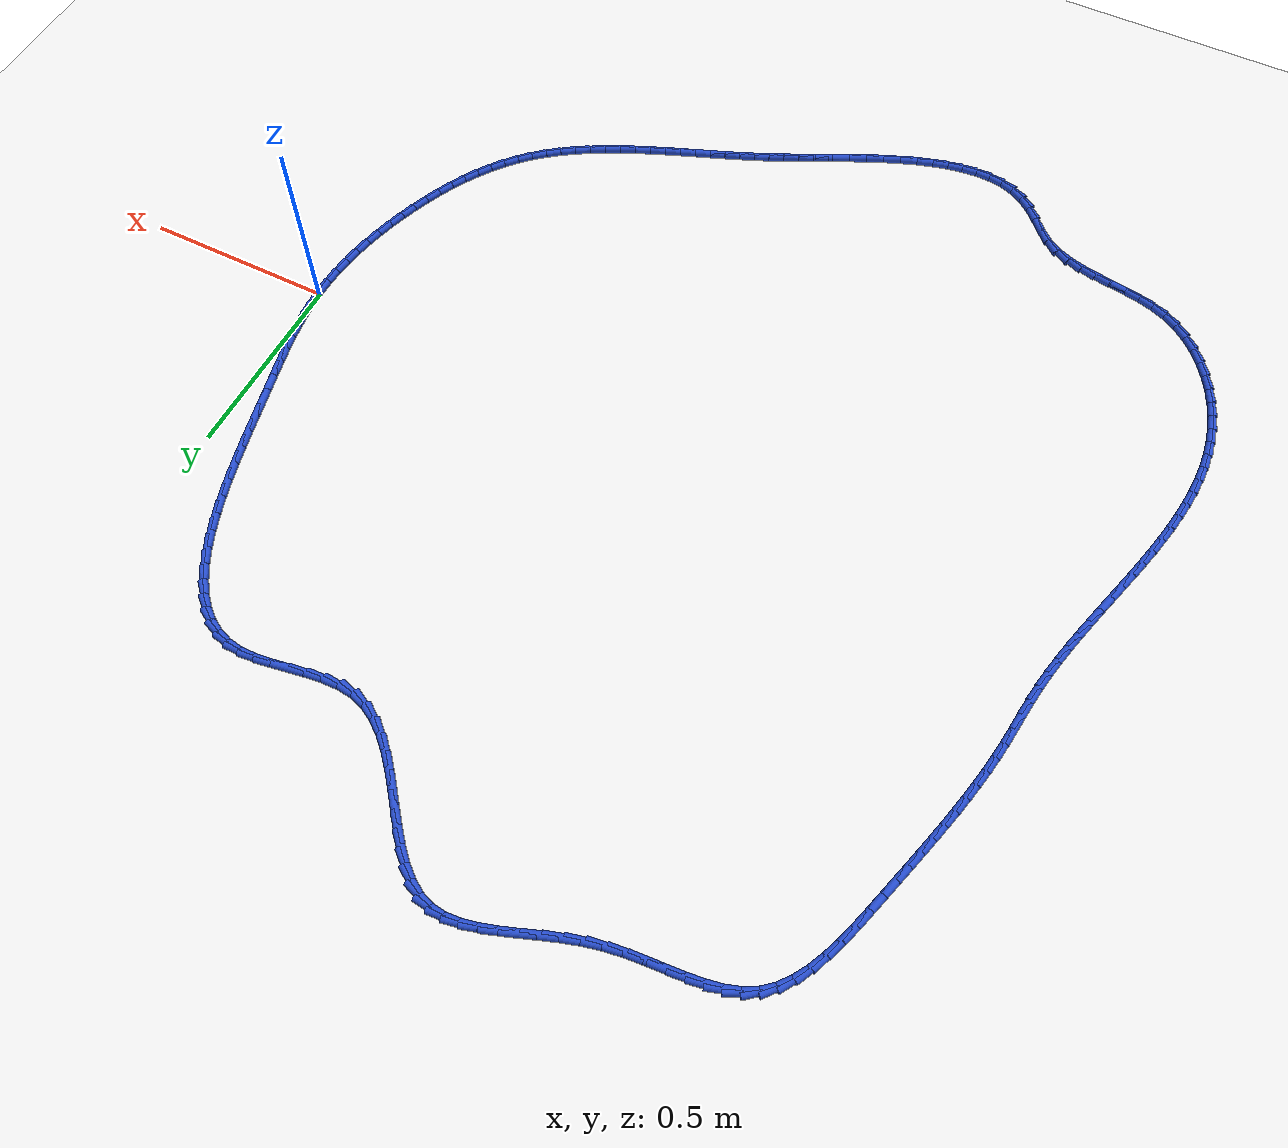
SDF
<sdf version="1.6">
 <world name="default">
  <light name="sun" type="directional">
   <pose>0 0 10 0 -0 0</pose>
   <diffuse>0.8 0.8 0.8 1</diffuse>
   <specular>0.2 0.2 0.2 1</specular>
   <attenuation>
    <range>1000</range>
    <constant>0.9</constant>
    <linear>0.01</linear>
    <quadratic>0.001</quadratic>
   </attenuation>
   <direction>-0.5 0.1 -0.9</direction>
  </light>
  <model name="ground_plane">
   <static>1</static>
   <link name="link">
    <collision name="collision">
     <geometry><plane><normal>0 0 1</normal><size>100 100</size></plane></geometry>
     <surface><friction><ode><mu>100</mu><mu2>50</mu2></ode></friction></surface>
    </collision>
    <visual name="visual">
     <cast_shadows>0</cast_shadows>
     <geometry><plane><normal>0 0 1</normal><size>100 100</size></plane></geometry>
     <material>
      <script><uri>file://media/materials/scripts/gazebo.material</uri><name>Gazebo/WhiteGlow</name></script>
     </material>
    </visual>
   </link>
  </model>
  <gravity>0 0 -9.8</gravity>
  <magnetic_field>6e-06 2.3e-05 -4.2e-05</magnetic_field>
  <atmosphere type="adiabatic"/>
  <physics name="default_physics" default="0" type="ode">
   <max_step_size>0.001</max_step_size>
   <real_time_factor>1</real_time_factor>
   <real_time_update_rate>1000</real_time_update_rate>
  </physics>
  <scene><ambient>0.4 0.4 0.4 1</ambient><background>0.7 0.7 0.7 1</background><shadows>1</shadows></scene>
  <spherical_coordinates>
   <surface_model>EARTH_WGS84</surface_model>
   <latitude_deg>0</latitude_deg>
   <longitude_deg>0</longitude_deg>
   <elevation>0</elevation>
   <heading_deg>0</heading_deg>
  </spherical_coordinates>
  <model name="line">
   <link name="link_0">
    <pose>1.3877787807814457e-17 -2.0816681711721685e-17 0.01 0 1.57 -1.5244611775396544</pose>
    <collision name="collision">
     <geometry><cylinder><radius>0.01</radius><length>0.08</length></cylinder></geometry>
    </collision>
    <visual name="visual">
     <material>
      <script><name>Gazebo/Blue</name><uri>file://media/materials/scripts/gazebo.material</uri></script>
     </material>
     <geometry><cylinder><radius>0.01</radius><length>0.08</length></cylinder></geometry>
    </visual>
   </link>
   <link name="link_1">
    <pose>-0.0017946024913230137 0.03870318821399723 0.01 0 1.57 -1.475856947605936</pose>
    <collision name="collision">
     <geometry><cylinder><radius>0.01</radius><length>0.08</length></cylinder></geometry>
    </collision>
    <visual name="visual">
     <material>
      <script><name>Gazebo/Blue</name><uri>file://media/materials/scripts/gazebo.material</uri></script>
     </material>
     <geometry><cylinder><radius>0.01</radius><length>0.08</length></cylinder></geometry>
    </visual>
   </link>
   <link name="link_2">
    <pose>-0.005453563407093402 0.07712729636301198 0.01 0 1.57 -1.433615060833195</pose>
    <collision name="collision">
     <geometry><cylinder><radius>0.01</radius><length>0.08</length></cylinder></geometry>
    </collision>
    <visual name="visual">
     <material>
      <script><name>Gazebo/Blue</name><uri>file://media/materials/scripts/gazebo.material</uri></script>
     </material>
     <geometry><cylinder><radius>0.01</radius><length>0.08</length></cylinder></geometry>
    </visual>
   </link>
   <link name="link_3">
    <pose>-0.010755834224982639 0.11553610068322581 0.01 0 1.57 -1.3985671574226302</pose>
    <collision name="collision">
     <geometry><cylinder><radius>0.01</radius><length>0.08</length></cylinder></geometry>
    </collision>
    <visual name="visual">
     <material>
      <script><name>Gazebo/Blue</name><uri>file://media/materials/scripts/gazebo.material</uri></script>
     </material>
     <geometry><cylinder><radius>0.01</radius><length>0.08</length></cylinder></geometry>
    </visual>
   </link>
   <link name="link_4">
    <pose>-0.01748036642266225 0.15419337741082034 0.01 0 1.57 -1.371147287391011</pose>
    <collision name="collision">
     <geometry><cylinder><radius>0.01</radius><length>0.08</length></cylinder></geometry>
    </collision>
    <visual name="visual">
     <material>
      <script><name>Gazebo/Blue</name><uri>file://media/materials/scripts/gazebo.material</uri></script>
     </material>
     <geometry><cylinder><radius>0.01</radius><length>0.08</length></cylinder></geometry>
    </visual>
   </link>
   <link name="link_5">
    <pose>-0.025406111477803712 0.1933629027819771 0.01 0 1.57 -1.3514327908160615</pose>
    <collision name="collision">
     <geometry><cylinder><radius>0.01</radius><length>0.08</length></cylinder></geometry>
    </collision>
    <visual name="visual">
     <material>
      <script><name>Gazebo/Blue</name><uri>file://media/materials/scripts/gazebo.material</uri></script>
     </material>
     <geometry><cylinder><radius>0.01</radius><length>0.08</length></cylinder></geometry>
    </visual>
   </link>
   <link name="link_6">
    <pose>-0.034312020868078504 0.23330845303287756 0.01 0 1.57 -1.3392106671136177</pose>
    <collision name="collision">
     <geometry><cylinder><radius>0.01</radius><length>0.08</length></cylinder></geometry>
    </collision>
    <visual name="visual">
     <material>
      <script><name>Gazebo/Blue</name><uri>file://media/materials/scripts/gazebo.material</uri></script>
     </material>
     <geometry><cylinder><radius>0.01</radius><length>0.08</length></cylinder></geometry>
    </visual>
   </link>
   <link name="link_7">
    <pose>-0.04397704607115816 0.2742938043997033 0.01 0 1.57 -1.3340499072407581</pose>
    <collision name="collision">
     <geometry><cylinder><radius>0.01</radius><length>0.08</length></cylinder></geometry>
    </collision>
    <visual name="visual">
     <material>
      <script><name>Gazebo/Blue</name><uri>file://media/materials/scripts/gazebo.material</uri></script>
     </material>
     <geometry><cylinder><radius>0.01</radius><length>0.08</length></cylinder></geometry>
    </visual>
   </link>
   <link name="link_8">
    <pose>-0.054180138564714174 0.31658273311863605 0.01 0 1.57 -1.3352256575642685</pose>
    <collision name="collision">
     <geometry><cylinder><radius>0.01</radius><length>0.08</length></cylinder></geometry>
    </collision>
    <visual name="visual">
     <material>
      <script><name>Gazebo/Blue</name><uri>file://media/materials/scripts/gazebo.material</uri></script>
     </material>
     <geometry><cylinder><radius>0.01</radius><length>0.08</length></cylinder></geometry>
    </visual>
   </link>
   <link name="link_9">
    <pose>-0.06470471937124396 0.3604301895524924 0.01 0 1.57 -1.3372267925610564</pose>
    <collision name="collision">
     <geometry><cylinder><radius>0.01</radius><length>0.08</length></cylinder></geometry>
    </collision>
    <visual name="visual">
     <material>
      <script><name>Gazebo/Blue</name><uri>file://media/materials/scripts/gazebo.material</uri></script>
     </material>
     <geometry><cylinder><radius>0.01</radius><length>0.08</length></cylinder></geometry>
    </visual>
   </link>
   <link name="link_10">
    <pose>-0.07549326747762965 0.4057770371702371 0.01 0 1.57 -1.334056104778429</pose>
    <collision name="collision">
     <geometry><cylinder><radius>0.01</radius><length>0.08</length></cylinder></geometry>
    </collision>
    <visual name="visual">
     <material>
      <script><name>Gazebo/Blue</name><uri>file://media/materials/scripts/gazebo.material</uri></script>
     </material>
     <geometry><cylinder><radius>0.01</radius><length>0.08</length></cylinder></geometry>
    </visual>
   </link>
   <link name="link_11">
    <pose>-0.08668676271634951 0.4521721658967152 0.01 0 1.57 -1.325617531100941</pose>
    <collision name="collision">
     <geometry><cylinder><radius>0.01</radius><length>0.08</length></cylinder></geometry>
    </collision>
    <visual name="visual">
     <material>
      <script><name>Gazebo/Blue</name><uri>file://media/materials/scripts/gazebo.material</uri></script>
     </material>
     <geometry><cylinder><radius>0.01</radius><length>0.08</length></cylinder></geometry>
    </visual>
   </link>
   <link name="link_12">
    <pose>-0.09843866459206883 0.49913982243007937 0.01 0 1.57 -1.3119155089145758</pose>
    <collision name="collision">
     <geometry><cylinder><radius>0.01</radius><length>0.08</length></cylinder></geometry>
    </collision>
    <visual name="visual">
     <material>
      <script><name>Gazebo/Blue</name><uri>file://media/materials/scripts/gazebo.material</uri></script>
     </material>
     <geometry><cylinder><radius>0.01</radius><length>0.08</length></cylinder></geometry>
    </visual>
   </link>
   <link name="link_13">
    <pose>-0.11090243260945296 0.5462042534684828 0.01 0 1.57 -1.2926869284423528</pose>
    <collision name="collision">
     <geometry><cylinder><radius>0.01</radius><length>0.08</length></cylinder></geometry>
    </collision>
    <visual name="visual">
     <material>
      <script><name>Gazebo/Blue</name><uri>file://media/materials/scripts/gazebo.material</uri></script>
     </material>
     <geometry><cylinder><radius>0.01</radius><length>0.08</length></cylinder></geometry>
    </visual>
   </link>
   <link name="link_14">
    <pose>-0.12423152627316712 0.5928897057100778 0.01 0 1.57 -1.2673991050727702</pose>
    <collision name="collision">
     <geometry><cylinder><radius>0.01</radius><length>0.08</length></cylinder></geometry>
    </collision>
    <visual name="visual">
     <material>
      <script><name>Gazebo/Blue</name><uri>file://media/materials/scripts/gazebo.material</uri></script>
     </material>
     <geometry><cylinder><radius>0.01</radius><length>0.08</length></cylinder></geometry>
    </visual>
   </link>
   <link name="link_15">
    <pose>-0.13857940508787667 0.638720425853018 0.01 0 1.57 -1.2352221715384317</pose>
    <collision name="collision">
     <geometry><cylinder><radius>0.01</radius><length>0.08</length></cylinder></geometry>
    </collision>
    <visual name="visual">
     <material>
      <script><name>Gazebo/Blue</name><uri>file://media/materials/scripts/gazebo.material</uri></script>
     </material>
     <geometry><cylinder><radius>0.01</radius><length>0.08</length></cylinder></geometry>
    </visual>
   </link>
   <link name="link_16">
    <pose>-0.15409952855824682 0.6832206605954558 0.01 0 1.57 -1.194978563401989</pose>
    <collision name="collision">
     <geometry><cylinder><radius>0.01</radius><length>0.08</length></cylinder></geometry>
    </collision>
    <visual name="visual">
     <material>
      <script><name>Gazebo/Blue</name><uri>file://media/materials/scripts/gazebo.material</uri></script>
     </material>
     <geometry><cylinder><radius>0.01</radius><length>0.08</length></cylinder></geometry>
    </visual>
   </link>
   <link name="link_17">
    <pose>-0.1709453561889429 0.7259146566355439 0.01 0 1.57 -1.145073635421471</pose>
    <collision name="collision">
     <geometry><cylinder><radius>0.01</radius><length>0.08</length></cylinder></geometry>
    </collision>
    <visual name="visual">
     <material>
      <script><name>Gazebo/Blue</name><uri>file://media/materials/scripts/gazebo.material</uri></script>
     </material>
     <geometry><cylinder><radius>0.01</radius><length>0.08</length></cylinder></geometry>
    </visual>
   </link>
   <link name="link_18">
    <pose>-0.18927034748463029 0.7663266606714356 0.01 0 1.57 -1.0834199719086508</pose>
    <collision name="collision">
     <geometry><cylinder><radius>0.01</radius><length>0.08</length></cylinder></geometry>
    </collision>
    <visual name="visual">
     <material>
      <script><name>Gazebo/Blue</name><uri>file://media/materials/scripts/gazebo.material</uri></script>
     </material>
     <geometry><cylinder><radius>0.01</radius><length>0.08</length></cylinder></geometry>
    </visual>
   </link>
   <link name="link_19">
    <pose>-0.20922796194997412 0.8039809194012835 0.01 0 1.57 -1.0073913971181214</pose>
    <collision name="collision">
     <geometry><cylinder><radius>0.01</radius><length>0.08</length></cylinder></geometry>
    </collision>
    <visual name="visual">
     <material>
      <script><name>Gazebo/Blue</name><uri>file://media/materials/scripts/gazebo.material</uri></script>
     </material>
     <geometry><cylinder><radius>0.01</radius><length>0.08</length></cylinder></geometry>
    </visual>
   </link>
   <link name="link_20">
    <pose>-0.2309716590896398 0.8384016795232405 0.01 0 1.57 -0.9138948361387474</pose>
    <collision name="collision">
     <geometry><cylinder><radius>0.01</radius><length>0.08</length></cylinder></geometry>
    </collision>
    <visual name="visual">
     <material>
      <script><name>Gazebo/Blue</name><uri>file://media/materials/scripts/gazebo.material</uri></script>
     </material>
     <geometry><cylinder><radius>0.01</radius><length>0.08</length></cylinder></geometry>
    </visual>
   </link>
   <link name="link_21">
    <pose>-0.25465489840829264 0.8691131877354601 0.01 0 1.57 -0.799741780718439</pose>
    <collision name="collision">
     <geometry><cylinder><radius>0.01</radius><length>0.08</length></cylinder></geometry>
    </collision>
    <visual name="visual">
     <material>
      <script><name>Gazebo/Blue</name><uri>file://media/materials/scripts/gazebo.material</uri></script>
     </material>
     <geometry><cylinder><radius>0.01</radius><length>0.08</length></cylinder></geometry>
    </visual>
   </link>
   <link name="link_22">
    <pose>-0.28043113941059783 0.8956396907360942 0.01 0 1.57 -0.6626045799479172</pose>
    <collision name="collision">
     <geometry><cylinder><radius>0.01</radius><length>0.08</length></cylinder></geometry>
    </collision>
    <visual name="visual">
     <material>
      <script><name>Gazebo/Blue</name><uri>file://media/materials/scripts/gazebo.material</uri></script>
     </material>
     <geometry><cylinder><radius>0.01</radius><length>0.08</length></cylinder></geometry>
    </visual>
   </link>
   <link name="link_23">
    <pose>-0.3084538416012208 0.9175054352232963 0.01 0 1.57 -0.5027622009771362</pose>
    <collision name="collision">
     <geometry><cylinder><radius>0.01</radius><length>0.08</length></cylinder></geometry>
    </collision>
    <visual name="visual">
     <material>
      <script><name>Gazebo/Blue</name><uri>file://media/materials/scripts/gazebo.material</uri></script>
     </material>
     <geometry><cylinder><radius>0.01</radius><length>0.08</length></cylinder></geometry>
    </visual>
   </link>
   <link name="link_24">
    <pose>-0.33887646448482656 0.9342346678952188 0.01 0 1.57 -0.32515732627907473</pose>
    <collision name="collision">
     <geometry><cylinder><radius>0.01</radius><length>0.08</length></cylinder></geometry>
    </collision>
    <visual name="visual">
     <material>
      <script><name>Gazebo/Blue</name><uri>file://media/materials/scripts/gazebo.material</uri></script>
     </material>
     <geometry><cylinder><radius>0.01</radius><length>0.08</length></cylinder></geometry>
    </visual>
   </link>
   <link name="link_25">
    <pose>-0.3718524675660807 0.9453516354500151 0.01 0 1.57 -0.1401075279615521</pose>
    <collision name="collision">
     <geometry><cylinder><radius>0.01</radius><length>0.08</length></cylinder></geometry>
    </collision>
    <visual name="visual">
     <material>
      <script><name>Gazebo/Blue</name><uri>file://media/materials/scripts/gazebo.material</uri></script>
     </material>
     <geometry><cylinder><radius>0.01</radius><length>0.08</length></cylinder></geometry>
    </visual>
   </link>
   <link name="link_26">
    <pose>-0.40753412628165114 0.9503838754427036 0.01 0 1.57 0.021815216355873506</pose>
    <collision name="collision">
     <geometry><cylinder><radius>0.01</radius><length>0.08</length></cylinder></geometry>
    </collision>
    <visual name="visual">
     <material>
      <script><name>Gazebo/Blue</name><uri>file://media/materials/scripts/gazebo.material</uri></script>
     </material>
     <geometry><cylinder><radius>0.01</radius><length>0.08</length></cylinder></geometry>
    </visual>
   </link>
   <link name="link_27">
    <pose>-0.44582563750177606 0.9495484053022043 0.01 0 1.57 0.12240143287835614</pose>
    <collision name="collision">
     <geometry><cylinder><radius>0.01</radius><length>0.08</length></cylinder></geometry>
    </collision>
    <visual name="visual">
     <material>
      <script><name>Gazebo/Blue</name><uri>file://media/materials/scripts/gazebo.material</uri></script>
     </material>
     <geometry><cylinder><radius>0.01</radius><length>0.08</length></cylinder></geometry>
    </visual>
   </link>
   <link name="link_28">
    <pose>-0.4860791408080133 0.9445965644073989 0.01 0 1.57 0.16970273421269255</pose>
    <collision name="collision">
     <geometry><cylinder><radius>0.01</radius><length>0.08</length></cylinder></geometry>
    </collision>
    <visual name="visual">
     <material>
      <script><name>Gazebo/Blue</name><uri>file://media/materials/scripts/gazebo.material</uri></script>
     </material>
     <geometry><cylinder><radius>0.01</radius><length>0.08</length></cylinder></geometry>
    </visual>
   </link>
   <link name="link_29">
    <pose>-0.5275723012861633 0.9374866776364873 0.01 0 1.57 0.17227022121737576</pose>
    <collision name="collision">
     <geometry><cylinder><radius>0.01</radius><length>0.08</length></cylinder></geometry>
    </collision>
    <visual name="visual">
     <material>
      <script><name>Gazebo/Blue</name><uri>file://media/materials/scripts/gazebo.material</uri></script>
     </material>
     <geometry><cylinder><radius>0.01</radius><length>0.08</length></cylinder></geometry>
    </visual>
   </link>
   <link name="link_30">
    <pose>-0.5695827840220269 0.9301770698676701 0.01 0 1.57 0.13200955417578925</pose>
    <collision name="collision">
     <geometry><cylinder><radius>0.01</radius><length>0.08</length></cylinder></geometry>
    </collision>
    <visual name="visual">
     <material>
      <script><name>Gazebo/Blue</name><uri>file://media/materials/scripts/gazebo.material</uri></script>
     </material>
     <geometry><cylinder><radius>0.01</radius><length>0.08</length></cylinder></geometry>
    </visual>
   </link>
   <link name="link_31">
    <pose>-0.6113882541014052 0.924626065979148 0.01 0 1.57 0.04483684213266937</pose>
    <collision name="collision">
     <geometry><cylinder><radius>0.01</radius><length>0.08</length></cylinder></geometry>
    </collision>
    <visual name="visual">
     <material>
      <script><name>Gazebo/Blue</name><uri>file://media/materials/scripts/gazebo.material</uri></script>
     </material>
     <geometry><cylinder><radius>0.01</radius><length>0.08</length></cylinder></geometry>
    </visual>
   </link>
   <link name="link_32">
    <pose>-0.6522663766100993 0.922791990849121 0.01 0 1.57 -0.09760704919171943</pose>
    <collision name="collision">
     <geometry><cylinder><radius>0.01</radius><length>0.08</length></cylinder></geometry>
    </collision>
    <visual name="visual">
     <material>
      <script><name>Gazebo/Blue</name><uri>file://media/materials/scripts/gazebo.material</uri></script>
     </material>
     <geometry><cylinder><radius>0.01</radius><length>0.08</length></cylinder></geometry>
    </visual>
   </link>
   <link name="link_33">
    <pose>-0.6914948166339101 0.9266331693557902 0.01 0 1.57 -0.29641620539197827</pose>
    <collision name="collision">
     <geometry><cylinder><radius>0.01</radius><length>0.08</length></cylinder></geometry>
    </collision>
    <visual name="visual">
     <material>
      <script><name>Gazebo/Blue</name><uri>file://media/materials/scripts/gazebo.material</uri></script>
     </material>
     <geometry><cylinder><radius>0.01</radius><length>0.08</length></cylinder></geometry>
    </visual>
   </link>
   <link name="link_34">
    <pose>-0.7284164575644547 0.9379095501245138 0.01 0 1.57 -0.4914064081527176</pose>
    <collision name="collision">
     <geometry><cylinder><radius>0.01</radius><length>0.08</length></cylinder></geometry>
    </collision>
    <visual name="visual">
     <material>
      <script><name>Gazebo/Blue</name><uri>file://media/materials/scripts/gazebo.material</uri></script>
     </material>
     <geometry><cylinder><radius>0.01</radius><length>0.08</length></cylinder></geometry>
    </visual>
   </link>
   <link name="link_35">
    <pose>-0.7630164923608376 0.9564273517110709 0.01 0 1.57 -0.6431609272816179</pose>
    <collision name="collision">
     <geometry><cylinder><radius>0.01</radius><length>0.08</length></cylinder></geometry>
    </collision>
    <visual name="visual">
     <material>
      <script><name>Gazebo/Blue</name><uri>file://media/materials/scripts/gazebo.material</uri></script>
     </material>
     <geometry><cylinder><radius>0.01</radius><length>0.08</length></cylinder></geometry>
    </visual>
   </link>
   <link name="link_36">
    <pose>-0.7956453997328672 0.9808816933022234 0.01 0 1.57 -0.7531336245590704</pose>
    <collision name="collision">
     <geometry><cylinder><radius>0.01</radius><length>0.08</length></cylinder></geometry>
    </collision>
    <visual name="visual">
     <material>
      <script><name>Gazebo/Blue</name><uri>file://media/materials/scripts/gazebo.material</uri></script>
     </material>
     <geometry><cylinder><radius>0.01</radius><length>0.08</length></cylinder></geometry>
    </visual>
   </link>
   <link name="link_37">
    <pose>-0.8266578770756408 1.0099548619976593 0.01 0 1.57 -0.8276030585605672</pose>
    <collision name="collision">
     <geometry><cylinder><radius>0.01</radius><length>0.08</length></cylinder></geometry>
    </collision>
    <visual name="visual">
     <material>
      <script><name>Gazebo/Blue</name><uri>file://media/materials/scripts/gazebo.material</uri></script>
     </material>
     <geometry><cylinder><radius>0.01</radius><length>0.08</length></cylinder></geometry>
    </visual>
   </link>
   <link name="link_38">
    <pose>-0.8564086217842543 1.042329144897065 0.01 0 1.57 -0.8724223237064609</pose>
    <collision name="collision">
     <geometry><cylinder><radius>0.01</radius><length>0.08</length></cylinder></geometry>
    </collision>
    <visual name="visual">
     <material>
      <script><name>Gazebo/Blue</name><uri>file://media/materials/scripts/gazebo.material</uri></script>
     </material>
     <geometry><cylinder><radius>0.01</radius><length>0.08</length></cylinder></geometry>
    </visual>
   </link>
   <link name="link_39">
    <pose>-0.8852523312538046 1.0766868291001277 0.01 0 1.57 -0.891326140688629</pose>
    <collision name="collision">
     <geometry><cylinder><radius>0.01</radius><length>0.08</length></cylinder></geometry>
    </collision>
    <visual name="visual">
     <material>
      <script><name>Gazebo/Blue</name><uri>file://media/materials/scripts/gazebo.material</uri></script>
     </material>
     <geometry><cylinder><radius>0.01</radius><length>0.08</length></cylinder></geometry>
    </visual>
   </link>
   <link name="link_40">
    <pose>-0.9135437028793886 1.1117102017065348 0.01 0 1.57 -0.885559882948281</pose>
    <collision name="collision">
     <geometry><cylinder><radius>0.01</radius><length>0.08</length></cylinder></geometry>
    </collision>
    <visual name="visual">
     <material>
      <script><name>Gazebo/Blue</name><uri>file://media/materials/scripts/gazebo.material</uri></script>
     </material>
     <geometry><cylinder><radius>0.01</radius><length>0.08</length></cylinder></geometry>
    </visual>
   </link>
   <link name="link_41">
    <pose>-0.9416374340561025 1.1460815498159729 0.01 0 1.57 -0.8537278694690869</pose>
    <collision name="collision">
     <geometry><cylinder><radius>0.01</radius><length>0.08</length></cylinder></geometry>
    </collision>
    <visual name="visual">
     <material>
      <script><name>Gazebo/Blue</name><uri>file://media/materials/scripts/gazebo.material</uri></script>
     </material>
     <geometry><cylinder><radius>0.01</radius><length>0.08</length></cylinder></geometry>
    </visual>
   </link>
   <link name="link_42">
    <pose>-0.9698882221790432 1.1784831605281298 0.01 0 1.57 -0.7914733820420172</pose>
    <collision name="collision">
     <geometry><cylinder><radius>0.01</radius><length>0.08</length></cylinder></geometry>
    </collision>
    <visual name="visual">
     <material>
      <script><name>Gazebo/Blue</name><uri>file://media/materials/scripts/gazebo.material</uri></script>
     </material>
     <geometry><cylinder><radius>0.01</radius><length>0.08</length></cylinder></geometry>
    </visual>
   </link>
   <link name="link_43">
    <pose>-0.9986507646433075 1.2075973209426918 0.01 0 1.57 -0.6911055287473408</pose>
    <collision name="collision">
     <geometry><cylinder><radius>0.01</radius><length>0.08</length></cylinder></geometry>
    </collision>
    <visual name="visual">
     <material>
      <script><name>Gazebo/Blue</name><uri>file://media/materials/scripts/gazebo.material</uri></script>
     </material>
     <geometry><cylinder><radius>0.01</radius><length>0.08</length></cylinder></geometry>
    </visual>
   </link>
   <link name="link_44">
    <pose>-1.0282797588439916 1.2321063181593468 0.01 0 1.57 -0.5422297799987283</pose>
    <collision name="collision">
     <geometry><cylinder><radius>0.01</radius><length>0.08</length></cylinder></geometry>
    </collision>
    <visual name="visual">
     <material>
      <script><name>Gazebo/Blue</name><uri>file://media/materials/scripts/gazebo.material</uri></script>
     </material>
     <geometry><cylinder><radius>0.01</radius><length>0.08</length></cylinder></geometry>
    </visual>
   </link>
   <link name="link_45">
    <pose>-1.0591299021761929 1.250692439277782 0.01 0 1.57 -0.33669822958910356</pose>
    <collision name="collision">
     <geometry><cylinder><radius>0.01</radius><length>0.08</length></cylinder></geometry>
    </collision>
    <visual name="visual">
     <material>
      <script><name>Gazebo/Blue</name><uri>file://media/materials/scripts/gazebo.material</uri></script>
     </material>
     <geometry><cylinder><radius>0.01</radius><length>0.08</length></cylinder></geometry>
    </visual>
   </link>
   <link name="link_46">
    <pose>-1.0915551283535128 1.2620421205153682 0.01 0 1.57 -0.10427068698773985</pose>
    <collision name="collision">
     <geometry><cylinder><radius>0.01</radius><length>0.08</length></cylinder></geometry>
    </collision>
    <visual name="visual">
     <material>
      <script><name>Gazebo/Blue</name><uri>file://media/materials/scripts/gazebo.material</uri></script>
     </material>
     <geometry><cylinder><radius>0.01</radius><length>0.08</length></cylinder></geometry>
    </visual>
   </link>
   <link name="link_47">
    <pose>-1.1257657190127353 1.2656222666183277 0.01 0 1.57 0.08414568604706085</pose>
    <collision name="collision">
     <geometry><cylinder><radius>0.01</radius><length>0.08</length></cylinder></geometry>
    </collision>
    <visual name="visual">
     <material>
      <script><name>Gazebo/Blue</name><uri>file://media/materials/scripts/gazebo.material</uri></script>
     </material>
     <geometry><cylinder><radius>0.01</radius><length>0.08</length></cylinder></geometry>
    </visual>
   </link>
   <link name="link_48">
    <pose>-1.1616599783034802 1.2625947707788077 0.01 0 1.57 0.21693622017412617</pose>
    <collision name="collision">
     <geometry><cylinder><radius>0.01</radius><length>0.08</length></cylinder></geometry>
    </collision>
    <visual name="visual">
     <material>
      <script><name>Gazebo/Blue</name><uri>file://media/materials/scripts/gazebo.material</uri></script>
     </material>
     <geometry><cylinder><radius>0.01</radius><length>0.08</length></cylinder></geometry>
    </visual>
   </link>
   <link name="link_49">
    <pose>-1.1990952887892572 1.2543438551020984 0.01 0 1.57 0.3018186956501924</pose>
    <collision name="collision">
     <geometry><cylinder><radius>0.01</radius><length>0.08</length></cylinder></geometry>
    </collision>
    <visual name="visual">
     <material>
      <script><name>Gazebo/Blue</name><uri>file://media/materials/scripts/gazebo.material</uri></script>
     </material>
     <geometry><cylinder><radius>0.01</radius><length>0.08</length></cylinder></geometry>
    </visual>
   </link>
   <link name="link_50">
    <pose>-1.2379290330335748 1.2422537416934891 0.01 0 1.57 0.34804526673265695</pose>
    <collision name="collision">
     <geometry><cylinder><radius>0.01</radius><length>0.08</length></cylinder></geometry>
    </collision>
    <visual name="visual">
     <material>
      <script><name>Gazebo/Blue</name><uri>file://media/materials/scripts/gazebo.material</uri></script>
     </material>
     <geometry><cylinder><radius>0.01</radius><length>0.08</length></cylinder></geometry>
    </visual>
   </link>
   <link name="link_51">
    <pose>-1.2780185935999442 1.2277086526582692 0.01 0 1.57 0.36227283005892513</pose>
    <collision name="collision">
     <geometry><cylinder><radius>0.01</radius><length>0.08</length></cylinder></geometry>
    </collision>
    <visual name="visual">
     <material>
      <script><name>Gazebo/Blue</name><uri>file://media/materials/scripts/gazebo.material</uri></script>
     </material>
     <geometry><cylinder><radius>0.01</radius><length>0.08</length></cylinder></geometry>
    </visual>
   </link>
   <link name="link_52">
    <pose>-1.3192213530518744 1.2120928101017288 0.01 0 1.57 0.3480716349226639</pose>
    <collision name="collision">
     <geometry><cylinder><radius>0.01</radius><length>0.08</length></cylinder></geometry>
    </collision>
    <visual name="visual">
     <material>
      <script><name>Gazebo/Blue</name><uri>file://media/materials/scripts/gazebo.material</uri></script>
     </material>
     <geometry><cylinder><radius>0.01</radius><length>0.08</length></cylinder></geometry>
    </visual>
   </link>
   <link name="link_53">
    <pose>-1.3613946939528738 1.1967904361291561 0.01 0 1.57 0.3064142870911959</pose>
    <collision name="collision">
     <geometry><cylinder><radius>0.01</radius><length>0.08</length></cylinder></geometry>
    </collision>
    <visual name="visual">
     <material>
      <script><name>Gazebo/Blue</name><uri>file://media/materials/scripts/gazebo.material</uri></script>
     </material>
     <geometry><cylinder><radius>0.01</radius><length>0.08</length></cylinder></geometry>
    </visual>
   </link>
   <link name="link_54">
    <pose>-1.4043959988664527 1.1831857528458418 0.01 0 1.57 0.23663826849893943</pose>
    <collision name="collision">
     <geometry><cylinder><radius>0.01</radius><length>0.08</length></cylinder></geometry>
    </collision>
    <visual name="visual">
     <material>
      <script><name>Gazebo/Blue</name><uri>file://media/materials/scripts/gazebo.material</uri></script>
     </material>
     <geometry><cylinder><radius>0.01</radius><length>0.08</length></cylinder></geometry>
    </visual>
   </link>
   <link name="link_55">
    <pose>-1.4480807611923703 1.1726508856167719 0.01 0 1.57 0.1578664580977036</pose>
    <collision name="collision">
     <geometry><cylinder><radius>0.01</radius><length>0.08</length></cylinder></geometry>
    </collision>
    <visual name="visual">
     <material>
      <script><name>Gazebo/Blue</name><uri>file://media/materials/scripts/gazebo.material</uri></script>
     </material>
     <geometry><cylinder><radius>0.01</radius><length>0.08</length></cylinder></geometry>
    </visual>
   </link>
   <link name="link_56">
    <pose>-1.4921601531029245 1.1656338385351133 0.01 0 1.57 0.10455293039260276</pose>
    <collision name="collision">
     <geometry><cylinder><radius>0.01</radius><length>0.08</length></cylinder></geometry>
    </collision>
    <visual name="visual">
     <material>
      <script><name>Gazebo/Blue</name><uri>file://media/materials/scripts/gazebo.material</uri></script>
     </material>
     <geometry><cylinder><radius>0.01</radius><length>0.08</length></cylinder></geometry>
    </visual>
   </link>
   <link name="link_57">
    <pose>-1.5361017486469897 1.1610228021336972 0.01 0 1.57 0.07999688228701433</pose>
    <collision name="collision">
     <geometry><cylinder><radius>0.01</radius><length>0.08</length></cylinder></geometry>
    </collision>
    <visual name="visual">
     <material>
      <script><name>Gazebo/Blue</name><uri>file://media/materials/scripts/gazebo.material</uri></script>
     </material>
     <geometry><cylinder><radius>0.01</radius><length>0.08</length></cylinder></geometry>
    </visual>
   </link>
   <link name="link_58">
    <pose>-1.579349655328273 1.15755570537991 0.01 0 1.57 0.08515951661189157</pose>
    <collision name="collision">
     <geometry><cylinder><radius>0.01</radius><length>0.08</length></cylinder></geometry>
    </collision>
    <visual name="visual">
     <material>
      <script><name>Gazebo/Blue</name><uri>file://media/materials/scripts/gazebo.material</uri></script>
     </material>
     <geometry><cylinder><radius>0.01</radius><length>0.08</length></cylinder></geometry>
    </visual>
   </link>
   <link name="link_59">
    <pose>-1.6213479806504802 1.153970477241138 0.01 0 1.57 0.12291733806011056</pose>
    <collision name="collision">
     <geometry><cylinder><radius>0.01</radius><length>0.08</length></cylinder></geometry>
    </collision>
    <visual name="visual">
     <material>
      <script><name>Gazebo/Blue</name><uri>file://media/materials/scripts/gazebo.material</uri></script>
     </material>
     <geometry><cylinder><radius>0.01</radius><length>0.08</length></cylinder></geometry>
    </visual>
   </link>
   <link name="link_60">
    <pose>-1.6615408321173193 1.1490050466847674 0.01 0 1.57 0.19844775259243733</pose>
    <collision name="collision">
     <geometry><cylinder><radius>0.01</radius><length>0.08</length></cylinder></geometry>
    </collision>
    <visual name="visual">
     <material>
      <script><name>Gazebo/Blue</name><uri>file://media/materials/scripts/gazebo.material</uri></script>
     </material>
     <geometry><cylinder><radius>0.01</radius><length>0.08</length></cylinder></geometry>
    </visual>
   </link>
   <link name="link_61">
    <pose>-1.6993723172324957 1.1413973426781845 0.01 0 1.57 0.31849839016324694</pose>
    <collision name="collision">
     <geometry><cylinder><radius>0.01</radius><length>0.08</length></cylinder></geometry>
    </collision>
    <visual name="visual">
     <material>
      <script><name>Gazebo/Blue</name><uri>file://media/materials/scripts/gazebo.material</uri></script>
     </material>
     <geometry><cylinder><radius>0.01</radius><length>0.08</length></cylinder></geometry>
    </visual>
   </link>
   <link name="link_62">
    <pose>-1.7342865434997168 1.1298852941887751 0.01 0 1.57 0.48772337726952136</pose>
    <collision name="collision">
     <geometry><cylinder><radius>0.01</radius><length>0.08</length></cylinder></geometry>
    </collision>
    <visual name="visual">
     <material>
      <script><name>Gazebo/Blue</name><uri>file://media/materials/scripts/gazebo.material</uri></script>
     </material>
     <geometry><cylinder><radius>0.01</radius><length>0.08</length></cylinder></geometry>
    </visual>
   </link>
   <link name="link_63">
    <pose>-1.7657276184226895 1.1132068301839255 0.01 0 1.57 0.6924582618871856</pose>
    <collision name="collision">
     <geometry><cylinder><radius>0.01</radius><length>0.08</length></cylinder></geometry>
    </collision>
    <visual name="visual">
     <material>
      <script><name>Gazebo/Blue</name><uri>file://media/materials/scripts/gazebo.material</uri></script>
     </material>
     <geometry><cylinder><radius>0.01</radius><length>0.08</length></cylinder></geometry>
    </visual>
   </link>
   <link name="link_64">
    <pose>-1.793264834079961 1.0903653350124758 0.01 0 1.57 0.873751924584222</pose>
    <collision name="collision">
     <geometry><cylinder><radius>0.01</radius><length>0.08</length></cylinder></geometry>
    </collision>
    <visual name="visual">
     <material>
      <script><name>Gazebo/Blue</name><uri>file://media/materials/scripts/gazebo.material</uri></script>
     </material>
     <geometry><cylinder><radius>0.01</radius><length>0.08</length></cylinder></geometry>
    </visual>
   </link>
   <link name="link_65">
    <pose>-1.8171577487726231 1.0618279107667905 0.01 0 1.57 1.0131812327672665</pose>
    <collision name="collision">
     <geometry><cylinder><radius>0.01</radius><length>0.08</length></cylinder></geometry>
    </collision>
    <visual name="visual">
     <material>
      <script><name>Gazebo/Blue</name><uri>file://media/materials/scripts/gazebo.material</uri></script>
     </material>
     <geometry><cylinder><radius>0.01</radius><length>0.08</length></cylinder></geometry>
    </visual>
   </link>
   <link name="link_66">
    <pose>-1.8379025482146976 1.0285634307857414 0.01 0 1.57 1.1162224537519967</pose>
    <collision name="collision">
     <geometry><cylinder><radius>0.01</radius><length>0.08</length></cylinder></geometry>
    </collision>
    <visual name="visual">
     <material>
      <script><name>Gazebo/Blue</name><uri>file://media/materials/scripts/gazebo.material</uri></script>
     </material>
     <geometry><cylinder><radius>0.01</radius><length>0.08</length></cylinder></geometry>
    </visual>
   </link>
   <link name="link_67">
    <pose>-1.8559956288143367 0.9915412151876153 0.01 0 1.57 1.1899975276524515</pose>
    <collision name="collision">
     <geometry><cylinder><radius>0.01</radius><length>0.08</length></cylinder></geometry>
    </collision>
    <visual name="visual">
     <material>
      <script><name>Gazebo/Blue</name><uri>file://media/materials/scripts/gazebo.material</uri></script>
     </material>
     <geometry><cylinder><radius>0.01</radius><length>0.08</length></cylinder></geometry>
    </visual>
   </link>
   <link name="link_68">
    <pose>-1.8719333869796921 0.951730584090697 0.01 0 1.57 1.2403746727568596</pose>
    <collision name="collision">
     <geometry><cylinder><radius>0.01</radius><length>0.08</length></cylinder></geometry>
    </collision>
    <visual name="visual">
     <material>
      <script><name>Gazebo/Blue</name><uri>file://media/materials/scripts/gazebo.material</uri></script>
     </material>
     <geometry><cylinder><radius>0.01</radius><length>0.08</length></cylinder></geometry>
    </visual>
   </link>
   <link name="link_69">
    <pose>-1.8862122191189152 0.9101008576132709 0.01 0 1.57 1.2713152108671992</pose>
    <collision name="collision">
     <geometry><cylinder><radius>0.01</radius><length>0.08</length></cylinder></geometry>
    </collision>
    <visual name="visual">
     <material>
      <script><name>Gazebo/Blue</name><uri>file://media/materials/scripts/gazebo.material</uri></script>
     </material>
     <geometry><cylinder><radius>0.01</radius><length>0.08</length></cylinder></geometry>
    </visual>
   </link>
   <link name="link_70">
    <pose>-1.8993285216401588 0.867621355873624 0.01 0 1.57 1.284934702680093</pose>
    <collision name="collision">
     <geometry><cylinder><radius>0.01</radius><length>0.08</length></cylinder></geometry>
    </collision>
    <visual name="visual">
     <material>
      <script><name>Gazebo/Blue</name><uri>file://media/materials/scripts/gazebo.material</uri></script>
     </material>
     <geometry><cylinder><radius>0.01</radius><length>0.08</length></cylinder></geometry>
    </visual>
   </link>
   <link name="link_71">
    <pose>-1.9117786310994853 0.825261282123647 0.01 0 1.57 1.2858170743674202</pose>
    <collision name="collision">
     <geometry><cylinder><radius>0.01</radius><length>0.08</length></cylinder></geometry>
    </collision>
    <visual name="visual">
     <material>
      <script><name>Gazebo/Blue</name><uri>file://media/materials/scripts/gazebo.material</uri></script>
     </material>
     <geometry><cylinder><radius>0.01</radius><length>0.08</length></cylinder></geometry>
    </visual>
   </link>
   <link name="link_72">
    <pose>-1.9239382383706742 0.7837542684612345 0.01 0 1.57 1.28666281614848</pose>
    <collision name="collision">
     <geometry><cylinder><radius>0.01</radius><length>0.08</length></cylinder></geometry>
    </collision>
    <visual name="visual">
     <material>
      <script><name>Gazebo/Blue</name><uri>file://media/materials/scripts/gazebo.material</uri></script>
     </material>
     <geometry><cylinder><radius>0.01</radius><length>0.08</length></cylinder></geometry>
    </visual>
   </link>
   <link name="link_73">
    <pose>-1.935809415068716 0.7431044229906855 0.01 0 1.57 1.2900828143448344</pose>
    <collision name="collision">
     <geometry><cylinder><radius>0.01</radius><length>0.08</length></cylinder></geometry>
    </collision>
    <visual name="visual">
     <material>
      <script><name>Gazebo/Blue</name><uri>file://media/materials/scripts/gazebo.material</uri></script>
     </material>
     <geometry><cylinder><radius>0.01</radius><length>0.08</length></cylinder></geometry>
    </visual>
   </link>
   <link name="link_74">
    <pose>-1.9473221276702646 0.7031750622825623 0.01 0 1.57 1.2961984678249916</pose>
    <collision name="collision">
     <geometry><cylinder><radius>0.01</radius><length>0.08</length></cylinder></geometry>
    </collision>
    <visual name="visual">
     <material>
      <script><name>Gazebo/Blue</name><uri>file://media/materials/scripts/gazebo.material</uri></script>
     </material>
     <geometry><cylinder><radius>0.01</radius><length>0.08</length></cylinder></geometry>
    </visual>
   </link>
   <link name="link_75">
    <pose>-1.958406342651973 0.6638295029074285 0.01 0 1.57 1.3050942781145092</pose>
    <collision name="collision">
     <geometry><cylinder><radius>0.01</radius><length>0.08</length></cylinder></geometry>
    </collision>
    <visual name="visual">
     <material>
      <script><name>Gazebo/Blue</name><uri>file://media/materials/scripts/gazebo.material</uri></script>
     </material>
     <geometry><cylinder><radius>0.01</radius><length>0.08</length></cylinder></geometry>
    </visual>
   </link>
   <link name="link_76">
    <pose>-1.968992026490495 0.6249310614358464 0.01 0 1.57 1.316810926799928</pose>
    <collision name="collision">
     <geometry><cylinder><radius>0.01</radius><length>0.08</length></cylinder></geometry>
    </collision>
    <visual name="visual">
     <material>
      <script><name>Gazebo/Blue</name><uri>file://media/materials/scripts/gazebo.material</uri></script>
     </material>
     <geometry><cylinder><radius>0.01</radius><length>0.08</length></cylinder></geometry>
    </visual>
   </link>
   <link name="link_77">
    <pose>-1.9790091456624832 0.5863430544383781 0.01 0 1.57 1.3313389313057982</pose>
    <collision name="collision">
     <geometry><cylinder><radius>0.01</radius><length>0.08</length></cylinder></geometry>
    </collision>
    <visual name="visual">
     <material>
      <script><name>Gazebo/Blue</name><uri>file://media/materials/scripts/gazebo.material</uri></script>
     </material>
     <geometry><cylinder><radius>0.01</radius><length>0.08</length></cylinder></geometry>
    </visual>
   </link>
   <link name="link_78">
    <pose>-1.9883876666445914 0.5479287984855871 0.01 0 1.57 1.348613456572809</pose>
    <collision name="collision">
     <geometry><cylinder><radius>0.01</radius><length>0.08</length></cylinder></geometry>
    </collision>
    <visual name="visual">
     <material>
      <script><name>Gazebo/Blue</name><uri>file://media/materials/scripts/gazebo.material</uri></script>
     </material>
     <geometry><cylinder><radius>0.01</radius><length>0.08</length></cylinder></geometry>
    </visual>
   </link>
   <link name="link_79">
    <pose>-1.9970575559134733 0.509551610148036 0.01 0 1.57 1.3685109553980592</pose>
    <collision name="collision">
     <geometry><cylinder><radius>0.01</radius><length>0.08</length></cylinder></geometry>
    </collision>
    <visual name="visual">
     <material>
      <script><name>Gazebo/Blue</name><uri>file://media/materials/scripts/gazebo.material</uri></script>
     </material>
     <geometry><cylinder><radius>0.01</radius><length>0.08</length></cylinder></geometry>
    </visual>
   </link>
   <link name="link_80">
    <pose>-2.004948779945782 0.47107480599628687 0.01 0 1.57 1.3908483317824356</pose>
    <collision name="collision">
     <geometry><cylinder><radius>0.01</radius><length>0.08</length></cylinder></geometry>
    </collision>
    <visual name="visual">
     <material>
      <script><name>Gazebo/Blue</name><uri>file://media/materials/scripts/gazebo.material</uri></script>
     </material>
     <geometry><cylinder><radius>0.01</radius><length>0.08</length></cylinder></geometry>
    </visual>
   </link>
   <link name="link_81">
    <pose>-2.011991305218171 0.4323617026009032 0.01 0 1.57 1.415385228566214</pose>
    <collision name="collision">
     <geometry><cylinder><radius>0.01</radius><length>0.08</length></cylinder></geometry>
    </collision>
    <visual name="visual">
     <material>
      <script><name>Gazebo/Blue</name><uri>file://media/materials/scripts/gazebo.material</uri></script>
     </material>
     <geometry><cylinder><radius>0.01</radius><length>0.08</length></cylinder></geometry>
    </visual>
   </link>
   <link name="link_82">
    <pose>-2.0181150982072933 0.39327561653244747 0.01 0 1.57 1.4399738764803132</pose>
    <collision name="collision">
     <geometry><cylinder><radius>0.01</radius><length>0.08</length></cylinder></geometry>
    </collision>
    <visual name="visual">
     <material>
      <script><name>Gazebo/Blue</name><uri>file://media/materials/scripts/gazebo.material</uri></script>
     </material>
     <geometry><cylinder><radius>0.01</radius><length>0.08</length></cylinder></geometry>
    </visual>
   </link>
   <link name="link_83">
    <pose>-2.0233217086849318 0.3537038637377302 0.01 0 1.57 1.4519085063891006</pose>
    <collision name="collision">
     <geometry><cylinder><radius>0.01</radius><length>0.08</length></cylinder></geometry>
    </collision>
    <visual name="visual">
     <material>
      <script><name>Gazebo/Blue</name><uri>file://media/materials/scripts/gazebo.material</uri></script>
     </material>
     <geometry><cylinder><radius>0.01</radius><length>0.08</length></cylinder></geometry>
    </visual>
   </link>
   <link name="link_84">
    <pose>-2.0281005359758533 0.3136973190630746 0.01 0 1.57 1.4463514690864652</pose>
    <collision name="collision">
     <geometry><cylinder><radius>0.01</radius><length>0.08</length></cylinder></geometry>
    </collision>
    <visual name="visual">
     <material>
      <script><name>Gazebo/Blue</name><uri>file://media/materials/scripts/gazebo.material</uri></script>
     </material>
     <geometry><cylinder><radius>0.01</radius><length>0.08</length></cylinder></geometry>
    </visual>
   </link>
   <link name="link_85">
    <pose>-2.033144494877859 0.273375088977849 0.01 0 1.57 1.4237324200178538</pose>
    <collision name="collision">
     <geometry><cylinder><radius>0.01</radius><length>0.08</length></cylinder></geometry>
    </collision>
    <visual name="visual">
     <material>
      <script><name>Gazebo/Blue</name><uri>file://media/materials/scripts/gazebo.material</uri></script>
     </material>
     <geometry><cylinder><radius>0.01</radius><length>0.08</length></cylinder></geometry>
    </visual>
   </link>
   <link name="link_86">
    <pose>-2.039146658129589 0.2328564485986555 0.01 0 1.57 1.3900089273853904</pose>
    <collision name="collision">
     <geometry><cylinder><radius>0.01</radius><length>0.08</length></cylinder></geometry>
    </collision>
    <visual name="visual">
     <material>
      <script><name>Gazebo/Blue</name><uri>file://media/materials/scripts/gazebo.material</uri></script>
     </material>
     <geometry><cylinder><radius>0.01</radius><length>0.08</length></cylinder></geometry>
    </visual>
   </link>
   <link name="link_87">
    <pose>-2.0465715702535596 0.19223501597412374 0.01 0 1.57 1.3595765101723378</pose>
    <collision name="collision">
     <geometry><cylinder><radius>0.01</radius><length>0.08</length></cylinder></geometry>
    </collision>
    <visual name="visual">
     <material>
      <script><name>Gazebo/Blue</name><uri>file://media/materials/scripts/gazebo.material</uri></script>
     </material>
     <geometry><cylinder><radius>0.01</radius><length>0.08</length></cylinder></geometry>
    </visual>
   </link>
   <link name="link_88">
    <pose>-2.0552976146788478 0.151538600320735 0.01 0 1.57 1.3345104978542286</pose>
    <collision name="collision">
     <geometry><cylinder><radius>0.01</radius><length>0.08</length></cylinder></geometry>
    </collision>
    <visual name="visual">
     <material>
      <script><name>Gazebo/Blue</name><uri>file://media/materials/scripts/gazebo.material</uri></script>
     </material>
     <geometry><cylinder><radius>0.01</radius><length>0.08</length></cylinder></geometry>
    </visual>
   </link>
   <link name="link_89">
    <pose>-2.0651105102949843 0.11078460732393372 0.01 0 1.57 1.3146155880673216</pose>
    <collision name="collision">
     <geometry><cylinder><radius>0.01</radius><length>0.08</length></cylinder></geometry>
    </collision>
    <visual name="visual">
     <material>
      <script><name>Gazebo/Blue</name><uri>file://media/materials/scripts/gazebo.material</uri></script>
     </material>
     <geometry><cylinder><radius>0.01</radius><length>0.08</length></cylinder></geometry>
    </visual>
   </link>
   <link name="link_90">
    <pose>-2.075795975991503 0.06999044266916296 0.01 0 1.57 1.2997194185854013</pose>
    <collision name="collision">
     <geometry><cylinder><radius>0.01</radius><length>0.08</length></cylinder></geometry>
    </collision>
    <visual name="visual">
     <material>
      <script><name>Gazebo/Blue</name><uri>file://media/materials/scripts/gazebo.material</uri></script>
     </material>
     <geometry><cylinder><radius>0.01</radius><length>0.08</length></cylinder></geometry>
    </visual>
   </link>
   <link name="link_91">
    <pose>-2.087139730657936 0.029173512041866433 0.01 0 1.57 1.2896849483638797</pose>
    <collision name="collision">
     <geometry><cylinder><radius>0.01</radius><length>0.08</length></cylinder></geometry>
    </collision>
    <visual name="visual">
     <material>
      <script><name>Gazebo/Blue</name><uri>file://media/materials/scripts/gazebo.material</uri></script>
     </material>
     <geometry><cylinder><radius>0.01</radius><length>0.08</length></cylinder></geometry>
    </visual>
   </link>
   <link name="link_92">
    <pose>-2.0989274931838175 -0.011648778872513216 0.01 0 1.57 1.2844184457454209</pose>
    <collision name="collision">
     <geometry><cylinder><radius>0.01</radius><length>0.08</length></cylinder></geometry>
    </collision>
    <visual name="visual">
     <material>
      <script><name>Gazebo/Blue</name><uri>file://media/materials/scripts/gazebo.material</uri></script>
     </material>
     <geometry><cylinder><radius>0.01</radius><length>0.08</length></cylinder></geometry>
    </visual>
   </link>
   <link name="link_93">
    <pose>-2.1109449824586792 -0.0524590243885307 0.01 0 1.57 1.2838743143817035</pose>
    <collision name="collision">
     <geometry><cylinder><radius>0.01</radius><length>0.08</length></cylinder></geometry>
    </collision>
    <visual name="visual">
     <material>
      <script><name>Gazebo/Blue</name><uri>file://media/materials/scripts/gazebo.material</uri></script>
     </material>
     <geometry><cylinder><radius>0.01</radius><length>0.08</length></cylinder></geometry>
    </visual>
   </link>
   <link name="link_94">
    <pose>-2.122977917372053 -0.09323981882074328 0.01 0 1.57 1.2880575933741467</pose>
    <collision name="collision">
     <geometry><cylinder><radius>0.01</radius><length>0.08</length></cylinder></geometry>
    </collision>
    <visual name="visual">
     <material>
      <script><name>Gazebo/Blue</name><uri>file://media/materials/scripts/gazebo.material</uri></script>
     </material>
     <geometry><cylinder><radius>0.01</radius><length>0.08</length></cylinder></geometry>
    </visual>
   </link>
   <link name="link_95">
    <pose>-2.1348120168134734 -0.13397375648370735 0.01 0 1.57 1.2970245586663993</pose>
    <collision name="collision">
     <geometry><cylinder><radius>0.01</radius><length>0.08</length></cylinder></geometry>
    </collision>
    <visual name="visual">
     <material>
      <script><name>Gazebo/Blue</name><uri>file://media/materials/scripts/gazebo.material</uri></script>
     </material>
     <geometry><cylinder><radius>0.01</radius><length>0.08</length></cylinder></geometry>
    </visual>
   </link>
   <link name="link_96">
    <pose>-2.1462329996724723 -0.17464343169197938 0.01 0 1.57 1.3108814419926507</pose>
    <collision name="collision">
     <geometry><cylinder><radius>0.01</radius><length>0.08</length></cylinder></geometry>
    </collision>
    <visual name="visual">
     <material>
      <script><name>Gazebo/Blue</name><uri>file://media/materials/scripts/gazebo.material</uri></script>
     </material>
     <geometry><cylinder><radius>0.01</radius><length>0.08</length></cylinder></geometry>
    </visual>
   </link>
   <link name="link_97">
    <pose>-2.157026584838583 -0.21523143876011577 0.01 0 1.57 1.3297808629015981</pose>
    <collision name="collision">
     <geometry><cylinder><radius>0.01</radius><length>0.08</length></cylinder></geometry>
    </collision>
    <visual name="visual">
     <material>
      <script><name>Gazebo/Blue</name><uri>file://media/materials/scripts/gazebo.material</uri></script>
     </material>
     <geometry><cylinder><radius>0.01</radius><length>0.08</length></cylinder></geometry>
    </visual>
   </link>
   <link name="link_98">
    <pose>-2.1669784912013372 -0.2557203720026737 0.01 0 1.57 1.3539151271240013</pose>
    <collision name="collision">
     <geometry><cylinder><radius>0.01</radius><length>0.08</length></cylinder></geometry>
    </collision>
    <visual name="visual">
     <material>
      <script><name>Gazebo/Blue</name><uri>file://media/materials/scripts/gazebo.material</uri></script>
     </material>
     <geometry><cylinder><radius>0.01</radius><length>0.08</length></cylinder></geometry>
    </visual>
   </link>
   <link name="link_99">
    <pose>-2.1758744376502688 -0.2960928257342079 0.01 0 1.57 1.3835050877571542</pose>
    <collision name="collision">
     <geometry><cylinder><radius>0.01</radius><length>0.08</length></cylinder></geometry>
    </collision>
    <visual name="visual">
     <material>
      <script><name>Gazebo/Blue</name><uri>file://media/materials/scripts/gazebo.material</uri></script>
     </material>
     <geometry><cylinder><radius>0.01</radius><length>0.08</length></cylinder></geometry>
    </visual>
   </link>
   <link name="link_100">
    <pose>-2.1835001430749106 -0.3363313942692759 0.01 0 1.57 1.4187828471021064</pose>
    <collision name="collision">
     <geometry><cylinder><radius>0.01</radius><length>0.08</length></cylinder></geometry>
    </collision>
    <visual name="visual">
     <material>
      <script><name>Gazebo/Blue</name><uri>file://media/materials/scripts/gazebo.material</uri></script>
     </material>
     <geometry><cylinder><radius>0.01</radius><length>0.08</length></cylinder></geometry>
    </visual>
   </link>
   <link name="link_101">
    <pose>-2.1896413263647947 -0.3764186719224338 0.01 0 1.57 1.4599663323045848</pose>
    <collision name="collision">
     <geometry><cylinder><radius>0.01</radius><length>0.08</length></cylinder></geometry>
    </collision>
    <visual name="visual">
     <material>
      <script><name>Gazebo/Blue</name><uri>file://media/materials/scripts/gazebo.material</uri></script>
     </material>
     <geometry><cylinder><radius>0.01</radius><length>0.08</length></cylinder></geometry>
    </visual>
   </link>
   <link name="link_102">
    <pose>-2.1940837064094536 -0.4163372530082382 0.01 0 1.57 1.507223967144351</pose>
    <collision name="collision">
     <geometry><cylinder><radius>0.01</radius><length>0.08</length></cylinder></geometry>
    </collision>
    <visual name="visual">
     <material>
      <script><name>Gazebo/Blue</name><uri>file://media/materials/scripts/gazebo.material</uri></script>
     </material>
     <geometry><cylinder><radius>0.01</radius><length>0.08</length></cylinder></geometry>
    </visual>
   </link>
   <link name="link_103">
    <pose>-2.1966130020984216 -0.4560697318412463 0.01 0 1.57 1.5606286861258687</pose>
    <collision name="collision">
     <geometry><cylinder><radius>0.01</radius><length>0.08</length></cylinder></geometry>
    </collision>
    <visual name="visual">
     <material>
      <script><name>Gazebo/Blue</name><uri>file://media/materials/scripts/gazebo.material</uri></script>
     </material>
     <geometry><cylinder><radius>0.01</radius><length>0.08</length></cylinder></geometry>
    </visual>
   </link>
   <link name="link_104">
    <pose>-2.19701493232123 -0.49559870273601286 0.01 0 1.57 -1.5214897894160782</pose>
    <collision name="collision">
     <geometry><cylinder><radius>0.01</radius><length>0.08</length></cylinder></geometry>
    </collision>
    <visual name="visual">
     <material>
      <script><name>Gazebo/Blue</name><uri>file://media/materials/scripts/gazebo.material</uri></script>
     </material>
     <geometry><cylinder><radius>0.01</radius><length>0.08</length></cylinder></geometry>
    </visual>
   </link>
   <link name="link_105">
    <pose>-2.1950752159674125 -0.5349067600070951 0.01 0 1.57 -1.4562330107730221</pose>
    <collision name="collision">
     <geometry><cylinder><radius>0.01</radius><length>0.08</length></cylinder></geometry>
    </collision>
    <visual name="visual">
     <material>
      <script><name>Gazebo/Blue</name><uri>file://media/materials/scripts/gazebo.material</uri></script>
     </material>
     <geometry><cylinder><radius>0.01</radius><length>0.08</length></cylinder></geometry>
    </visual>
   </link>
   <link name="link_106">
    <pose>-2.1905795719265013 -0.5739764979690495 0.01 0 1.57 -1.3857414494534996</pose>
    <collision name="collision">
     <geometry><cylinder><radius>0.01</radius><length>0.08</length></cylinder></geometry>
    </collision>
    <visual name="visual">
     <material>
      <script><name>Gazebo/Blue</name><uri>file://media/materials/scripts/gazebo.material</uri></script>
     </material>
     <geometry><cylinder><radius>0.01</radius><length>0.08</length></cylinder></geometry>
    </visual>
   </link>
   <link name="link_107">
    <pose>-2.183313719088029 -0.6127905109364322 0.01 0 1.57 -1.310853567188774</pose>
    <collision name="collision">
     <geometry><cylinder><radius>0.01</radius><length>0.08</length></cylinder></geometry>
    </collision>
    <visual name="visual">
     <material>
      <script><name>Gazebo/Blue</name><uri>file://media/materials/scripts/gazebo.material</uri></script>
     </material>
     <geometry><cylinder><radius>0.01</radius><length>0.08</length></cylinder></geometry>
    </visual>
   </link>
   <link name="link_108">
    <pose>-2.17306337634153 -0.6513313932238003 0.01 0 1.57 -1.2326900348705445</pose>
    <collision name="collision">
     <geometry><cylinder><radius>0.01</radius><length>0.08</length></cylinder></geometry>
    </collision>
    <visual name="visual">
     <material>
      <script><name>Gazebo/Blue</name><uri>file://media/materials/scripts/gazebo.material</uri></script>
     </material>
     <geometry><cylinder><radius>0.01</radius><length>0.08</length></cylinder></geometry>
    </visual>
   </link>
   <link name="link_109">
    <pose>-2.1596142631256194 -0.6895817379187853 0.01 0 1.57 -1.1526055256046976</pose>
    <collision name="collision">
     <geometry><cylinder><radius>0.01</radius><length>0.08</length></cylinder></geometry>
    </collision>
    <visual name="visual">
     <material>
      <script><name>Gazebo/Blue</name><uri>file://media/materials/scripts/gazebo.material</uri></script>
     </material>
     <geometry><cylinder><radius>0.01</radius><length>0.08</length></cylinder></geometry>
    </visual>
   </link>
   <link name="link_110">
    <pose>-2.1428091992440605 -0.7273965478057418 0.01 0 1.57 -1.0702884219444921</pose>
    <collision name="collision">
     <geometry><cylinder><radius>0.01</radius><length>0.08</length></cylinder></geometry>
    </collision>
    <visual name="visual">
     <material>
      <script><name>Gazebo/Blue</name><uri>file://media/materials/scripts/gazebo.material</uri></script>
     </material>
     <geometry><cylinder><radius>0.01</radius><length>0.08</length></cylinder></geometry>
    </visual>
   </link>
   <link name="link_111">
    <pose>-2.122705001128251 -0.7641526519384344 0.01 0 1.57 -0.9830266138469054</pose>
    <collision name="collision">
     <geometry><cylinder><radius>0.01</radius><length>0.08</length></cylinder></geometry>
    </collision>
    <visual name="visual">
     <material>
      <script><name>Gazebo/Blue</name><uri>file://media/materials/scripts/gazebo.material</uri></script>
     </material>
     <geometry><cylinder><radius>0.01</radius><length>0.08</length></cylinder></geometry>
    </visual>
   </link>
   <link name="link_112">
    <pose>-2.0994086075881837 -0.7991148813217593 0.01 0 1.57 -0.8879286716854582</pose>
    <collision name="collision">
     <geometry><cylinder><radius>0.01</radius><length>0.08</length></cylinder></geometry>
    </collision>
    <visual name="visual">
     <material>
      <script><name>Gazebo/Blue</name><uri>file://media/materials/scripts/gazebo.material</uri></script>
     </material>
     <geometry><cylinder><radius>0.01</radius><length>0.08</length></cylinder></geometry>
    </visual>
   </link>
   <link name="link_113">
    <pose>-2.0730269574338496 -0.8315480669606126 0.01 0 1.57 -0.7821349165562128</pose>
    <collision name="collision">
     <geometry><cylinder><radius>0.01</radius><length>0.08</length></cylinder></geometry>
    </collision>
    <visual name="visual">
     <material>
      <script><name>Gazebo/Blue</name><uri>file://media/materials/scripts/gazebo.material</uri></script>
     </material>
     <geometry><cylinder><radius>0.01</radius><length>0.08</length></cylinder></geometry>
    </visual>
   </link>
   <link name="link_114">
    <pose>-2.043666989475241 -0.8607170398598907 0.01 0 1.57 -0.6629881623210974</pose>
    <collision name="collision">
     <geometry><cylinder><radius>0.01</radius><length>0.08</length></cylinder></geometry>
    </collision>
    <visual name="visual">
     <material>
      <script><name>Gazebo/Blue</name><uri>file://media/materials/scripts/gazebo.material</uri></script>
     </material>
     <geometry><cylinder><radius>0.01</radius><length>0.08</length></cylinder></geometry>
    </visual>
   </link>
   <link name="link_115">
    <pose>-2.0114356425223505 -0.8858866310244898 0.01 0 1.57 -0.5285184583404248</pose>
    <collision name="collision">
     <geometry><cylinder><radius>0.01</radius><length>0.08</length></cylinder></geometry>
    </collision>
    <visual name="visual">
     <material>
      <script><name>Gazebo/Blue</name><uri>file://media/materials/scripts/gazebo.material</uri></script>
     </material>
     <geometry><cylinder><radius>0.01</radius><length>0.08</length></cylinder></geometry>
    </visual>
   </link>
   <link name="link_116">
    <pose>-1.9764398553851712 -0.9063216714593054 0.01 0 1.57 -0.383863636900376</pose>
    <collision name="collision">
     <geometry><cylinder><radius>0.01</radius><length>0.08</length></cylinder></geometry>
    </collision>
    <visual name="visual">
     <material>
      <script><name>Gazebo/Blue</name><uri>file://media/materials/scripts/gazebo.material</uri></script>
     </material>
     <geometry><cylinder><radius>0.01</radius><length>0.08</length></cylinder></geometry>
    </visual>
   </link>
   <link name="link_117">
    <pose>-1.938848947820997 -0.921504626728167 0.01 0 1.57 -0.26665422859862065</pose>
    <collision name="collision">
     <geometry><cylinder><radius>0.01</radius><length>0.08</length></cylinder></geometry>
    </collision>
    <visual name="visual">
     <material>
      <script><name>Gazebo/Blue</name><uri>file://media/materials/scripts/gazebo.material</uri></script>
     </material>
     <geometry><cylinder><radius>0.01</radius><length>0.08</length></cylinder></geometry>
    </visual>
   </link>
   <link name="link_118">
    <pose>-1.8992356478408152 -0.9323253725283114 0.01 0 1.57 -0.19098928004651008</pose>
    <collision name="collision">
     <geometry><cylinder><radius>0.01</radius><length>0.08</length></cylinder></geometry>
    </collision>
    <visual name="visual">
     <material>
      <script><name>Gazebo/Blue</name><uri>file://media/materials/scripts/gazebo.material</uri></script>
     </material>
     <geometry><cylinder><radius>0.01</radius><length>0.08</length></cylinder></geometry>
    </visual>
   </link>
   <link name="link_119">
    <pose>-1.8583331725212169 -0.9402336985774733 0.01 0 1.57 -0.1542741179452086</pose>
    <collision name="collision">
     <geometry><cylinder><radius>0.01</radius><length>0.08</length></cylinder></geometry>
    </collision>
    <visual name="visual">
     <material>
      <script><name>Gazebo/Blue</name><uri>file://media/materials/scripts/gazebo.material</uri></script>
     </material>
     <geometry><cylinder><radius>0.01</radius><length>0.08</length></cylinder></geometry>
    </visual>
   </link>
   <link name="link_120">
    <pose>-1.8168751498302491 -0.9466808281109141 0.01 0 1.57 -0.15469321888042956</pose>
    <collision name="collision">
     <geometry><cylinder><radius>0.01</radius><length>0.08</length></cylinder></geometry>
    </collision>
    <visual name="visual">
     <material>
      <script><name>Gazebo/Blue</name><uri>file://media/materials/scripts/gazebo.material</uri></script>
     </material>
     <geometry><cylinder><radius>0.01</radius><length>0.08</length></cylinder></geometry>
    </visual>
   </link>
   <link name="link_121">
    <pose>-1.7755952077359631 -0.9531179843638953 0.01 0 1.57 -0.192740794334783</pose>
    <collision name="collision">
     <geometry><cylinder><radius>0.01</radius><length>0.08</length></cylinder></geometry>
    </collision>
    <visual name="visual">
     <material>
      <script><name>Gazebo/Blue</name><uri>file://media/materials/scripts/gazebo.material</uri></script>
     </material>
     <geometry><cylinder><radius>0.01</radius><length>0.08</length></cylinder></geometry>
    </visual>
   </link>
   <link name="link_122">
    <pose>-1.7352269742064061 -0.9609963905716782 0.01 0 1.57 -0.27129490708598075</pose>
    <collision name="collision">
     <geometry><cylinder><radius>0.01</radius><length>0.08</length></cylinder></geometry>
    </collision>
    <visual name="visual">
     <material>
      <script><name>Gazebo/Blue</name><uri>file://media/materials/scripts/gazebo.material</uri></script>
     </material>
     <geometry><cylinder><radius>0.01</radius><length>0.08</length></cylinder></geometry>
    </visual>
   </link>
   <link name="link_123">
    <pose>-1.6965040772096271 -0.9717672699695244 0.01 0 1.57 -0.3941173801980752</pose>
    <collision name="collision">
     <geometry><cylinder><radius>0.01</radius><length>0.08</length></cylinder></geometry>
    </collision>
    <visual name="visual">
     <material>
      <script><name>Gazebo/Blue</name><uri>file://media/materials/scripts/gazebo.material</uri></script>
     </material>
     <geometry><cylinder><radius>0.01</radius><length>0.08</length></cylinder></geometry>
    </visual>
   </link>
   <link name="link_124">
    <pose>-1.6601601447136745 -0.9868818457926956 0.01 0 1.57 -0.5616208743111429</pose>
    <collision name="collision">
     <geometry><cylinder><radius>0.01</radius><length>0.08</length></cylinder></geometry>
    </collision>
    <visual name="visual">
     <material>
      <script><name>Gazebo/Blue</name><uri>file://media/materials/scripts/gazebo.material</uri></script>
     </material>
     <geometry><cylinder><radius>0.01</radius><length>0.08</length></cylinder></geometry>
    </visual>
   </link>
   <link name="link_125">
    <pose>-1.6269288009775063 -1.007791333549619 0.01 0 1.57 -0.7388539475330934</pose>
    <collision name="collision">
     <geometry><cylinder><radius>0.01</radius><length>0.08</length></cylinder></geometry>
    </collision>
    <visual name="visual">
     <material>
      <script><name>Gazebo/Blue</name><uri>file://media/materials/scripts/gazebo.material</uri></script>
     </material>
     <geometry><cylinder><radius>0.01</radius><length>0.08</length></cylinder></geometry>
    </visual>
   </link>
   <link name="link_126">
    <pose>-1.5970807595069485 -1.034982606089437 0.01 0 1.57 -0.8264949304649177</pose>
    <collision name="collision">
     <geometry><cylinder><radius>0.01</radius><length>0.08</length></cylinder></geometry>
    </collision>
    <visual name="visual">
     <material>
      <script><name>Gazebo/Blue</name><uri>file://media/materials/scripts/gazebo.material</uri></script>
     </material>
     <geometry><cylinder><radius>0.01</radius><length>0.08</length></cylinder></geometry>
    </visual>
   </link>
   <link name="link_127">
    <pose>-1.5691450597184926 -1.0653142545427092 0.01 0 1.57 -0.8128147597120488</pose>
    <collision name="collision">
     <geometry><cylinder><radius>0.01</radius><length>0.08</length></cylinder></geometry>
    </collision>
    <visual name="visual">
     <material>
      <script><name>Gazebo/Blue</name><uri>file://media/materials/scripts/gazebo.material</uri></script>
     </material>
     <geometry><cylinder><radius>0.01</radius><length>0.08</length></cylinder></geometry>
    </visual>
   </link>
   <link name="link_128">
    <pose>-1.5412412002814215 -1.0947917085816001 0.01 0 1.57 -0.6935114997675901</pose>
    <collision name="collision">
     <geometry><cylinder><radius>0.01</radius><length>0.08</length></cylinder></geometry>
    </collision>
    <visual name="visual">
     <material>
      <script><name>Gazebo/Blue</name><uri>file://media/materials/scripts/gazebo.material</uri></script>
     </material>
     <geometry><cylinder><radius>0.01</radius><length>0.08</length></cylinder></geometry>
    </visual>
   </link>
   <link name="link_129">
    <pose>-1.51152419525033 -1.119494169624446 0.01 0 1.57 -0.5089508967885015</pose>
    <collision name="collision">
     <geometry><cylinder><radius>0.01</radius><length>0.08</length></cylinder></geometry>
    </collision>
    <visual name="visual">
     <material>
      <script><name>Gazebo/Blue</name><uri>file://media/materials/scripts/gazebo.material</uri></script>
     </material>
     <geometry><cylinder><radius>0.01</radius><length>0.08</length></cylinder></geometry>
    </visual>
   </link>
   <link name="link_130">
    <pose>-1.4791418114867851 -1.137562962516948 0.01 0 1.57 -0.328592848446487</pose>
    <collision name="collision">
     <geometry><cylinder><radius>0.01</radius><length>0.08</length></cylinder></geometry>
    </collision>
    <visual name="visual">
     <material>
      <script><name>Gazebo/Blue</name><uri>file://media/materials/scripts/gazebo.material</uri></script>
     </material>
     <geometry><cylinder><radius>0.01</radius><length>0.08</length></cylinder></geometry>
    </visual>
   </link>
   <link name="link_131">
    <pose>-1.4443434004355429 -1.1494275984088613 0.01 0 1.57 -0.16667306456227754</pose>
    <collision name="collision">
     <geometry><cylinder><radius>0.01</radius><length>0.08</length></cylinder></geometry>
    </collision>
    <visual name="visual">
     <material>
      <script><name>Gazebo/Blue</name><uri>file://media/materials/scripts/gazebo.material</uri></script>
     </material>
     <geometry><cylinder><radius>0.01</radius><length>0.08</length></cylinder></geometry>
    </visual>
   </link>
   <link name="link_132">
    <pose>-1.4074356691424432 -1.1556367261928435 0.01 0 1.57 -0.028467088495871182</pose>
    <collision name="collision">
     <geometry><cylinder><radius>0.01</radius><length>0.08</length></cylinder></geometry>
    </collision>
    <visual name="visual">
     <material>
      <script><name>Gazebo/Blue</name><uri>file://media/materials/scripts/gazebo.material</uri></script>
     </material>
     <geometry><cylinder><radius>0.01</radius><length>0.08</length></cylinder></geometry>
    </visual>
   </link>
   <link name="link_133">
    <pose>-1.3687253246533249 -1.156738994761552 0.01 0 1.57 0.08574458026779165</pose>
    <collision name="collision">
     <geometry><cylinder><radius>0.01</radius><length>0.08</length></cylinder></geometry>
    </collision>
    <visual name="visual">
     <material>
      <script><name>Gazebo/Blue</name><uri>file://media/materials/scripts/gazebo.material</uri></script>
     </material>
     <geometry><cylinder><radius>0.01</radius><length>0.08</length></cylinder></geometry>
    </visual>
   </link>
   <link name="link_134">
    <pose>-1.3285190740140262 -1.1532830530076446 0.01 0 1.57 0.17842804548551633</pose>
    <collision name="collision">
     <geometry><cylinder><radius>0.01</radius><length>0.08</length></cylinder></geometry>
    </collision>
    <visual name="visual">
     <material>
      <script><name>Gazebo/Blue</name><uri>file://media/materials/scripts/gazebo.material</uri></script>
     </material>
     <geometry><cylinder><radius>0.01</radius><length>0.08</length></cylinder></geometry>
    </visual>
   </link>
   <link name="link_135">
    <pose>-1.2871236242703863 -1.145817549823779 0.01 0 1.57 0.2529085985010577</pose>
    <collision name="collision">
     <geometry><cylinder><radius>0.01</radius><length>0.08</length></cylinder></geometry>
    </collision>
    <visual name="visual">
     <material>
      <script><name>Gazebo/Blue</name><uri>file://media/materials/scripts/gazebo.material</uri></script>
     </material>
     <geometry><cylinder><radius>0.01</radius><length>0.08</length></cylinder></geometry>
    </visual>
   </link>
   <link name="link_136">
    <pose>-1.2448456824682443 -1.1348911341026127 0.01 0 1.57 0.3123569400135349</pose>
    <collision name="collision">
     <geometry><cylinder><radius>0.01</radius><length>0.08</length></cylinder></geometry>
    </collision>
    <visual name="visual">
     <material>
      <script><name>Gazebo/Blue</name><uri>file://media/materials/scripts/gazebo.material</uri></script>
     </material>
     <geometry><cylinder><radius>0.01</radius><length>0.08</length></cylinder></geometry>
    </visual>
   </link>
   <link name="link_137">
    <pose>-1.201991955653438 -1.121052454736803 0.01 0 1.57 0.3594056940143235</pose>
    <collision name="collision">
     <geometry><cylinder><radius>0.01</radius><length>0.08</length></cylinder></geometry>
    </collision>
    <visual name="visual">
     <material>
      <script><name>Gazebo/Blue</name><uri>file://media/materials/scripts/gazebo.material</uri></script>
     </material>
     <geometry><cylinder><radius>0.01</radius><length>0.08</length></cylinder></geometry>
    </visual>
   </link>
   <link name="link_138">
    <pose>-1.1588691508718079 -1.1048501606190082 0.01 0 1.57 0.3960779422350284</pose>
    <collision name="collision">
     <geometry><cylinder><radius>0.01</radius><length>0.08</length></cylinder></geometry>
    </collision>
    <visual name="visual">
     <material>
      <script><name>Gazebo/Blue</name><uri>file://media/materials/scripts/gazebo.material</uri></script>
     </material>
     <geometry><cylinder><radius>0.01</radius><length>0.08</length></cylinder></geometry>
    </visual>
   </link>
   <link name="link_139">
    <pose>-1.115783975169193 -1.0868329006418858 0.01 0 1.57 0.4238302122448239</pose>
    <collision name="collision">
     <geometry><cylinder><radius>0.01</radius><length>0.08</length></cylinder></geometry>
    </collision>
    <visual name="visual">
     <material>
      <script><name>Gazebo/Blue</name><uri>file://media/materials/scripts/gazebo.material</uri></script>
     </material>
     <geometry><cylinder><radius>0.01</radius><length>0.08</length></cylinder></geometry>
    </visual>
   </link>
   <link name="link_140">
    <pose>-1.073043135591431 -1.067549323698093 0.01 0 1.57 0.4436148737290268</pose>
    <collision name="collision">
     <geometry><cylinder><radius>0.01</radius><length>0.08</length></cylinder></geometry>
    </collision>
    <visual name="visual">
     <material>
      <script><name>Gazebo/Blue</name><uri>file://media/materials/scripts/gazebo.material</uri></script>
     </material>
     <geometry><cylinder><radius>0.01</radius><length>0.08</length></cylinder></geometry>
    </visual>
   </link>
   <link name="link_141">
    <pose>-1.0309533391843613 -1.0475480786802878 0.01 0 1.57 0.4559206893814408</pose>
    <collision name="collision">
     <geometry><cylinder><radius>0.01</radius><length>0.08</length></cylinder></geometry>
    </collision>
    <visual name="visual">
     <material>
      <script><name>Gazebo/Blue</name><uri>file://media/materials/scripts/gazebo.material</uri></script>
     </material>
     <geometry><cylinder><radius>0.01</radius><length>0.08</length></cylinder></geometry>
    </visual>
   </link>
   <link name="link_142">
    <pose>-0.9898212929938225 -1.0273778144811276 0.01 0 1.57 0.460770775787071</pose>
    <collision name="collision">
     <geometry><cylinder><radius>0.01</radius><length>0.08</length></cylinder></geometry>
    </collision>
    <visual name="visual">
     <material>
      <script><name>Gazebo/Blue</name><uri>file://media/materials/scripts/gazebo.material</uri></script>
     </material>
     <geometry><cylinder><radius>0.01</radius><length>0.08</length></cylinder></geometry>
    </visual>
   </link>
   <link name="link_143">
    <pose>-0.9499537040656546 -1.0075871799932705 0.01 0 1.57 0.45774778597791105</pose>
    <collision name="collision">
     <geometry><cylinder><radius>0.01</radius><length>0.08</length></cylinder></geometry>
    </collision>
    <visual name="visual">
     <material>
      <script><name>Gazebo/Blue</name><uri>file://media/materials/scripts/gazebo.material</uri></script>
     </material>
     <geometry><cylinder><radius>0.01</radius><length>0.08</length></cylinder></geometry>
    </visual>
   </link>
   <link name="link_144">
    <pose>-0.9116397643461165 -0.9887119391561905 0.01 0 1.57 0.4483488529839349</pose>
    <collision name="collision">
     <geometry><cylinder><radius>0.01</radius><length>0.08</length></cylinder></geometry>
    </collision>
    <visual name="visual">
     <material>
      <script><name>Gazebo/Blue</name><uri>file://media/materials/scripts/gazebo.material</uri></script>
     </material>
     <geometry><cylinder><radius>0.01</radius><length>0.08</length></cylinder></geometry>
    </visual>
   </link>
   <link name="link_145">
    <pose>-0.8747003199793245 -0.9709433181174549 0.01 0 1.57 0.4349680616061425</pose>
    <collision name="collision">
     <geometry><cylinder><radius>0.01</radius><length>0.08</length></cylinder></geometry>
    </collision>
    <visual name="visual">
     <material>
      <script><name>Gazebo/Blue</name><uri>file://media/materials/scripts/gazebo.material</uri></script>
     </material>
     <geometry><cylinder><radius>0.01</radius><length>0.08</length></cylinder></geometry>
    </visual>
   </link>
   <link name="link_146">
    <pose>-0.838448305821981 -0.9540988989508503 0.01 0 1.57 0.41818291175574007</pose>
    <collision name="collision">
     <geometry><cylinder><radius>0.01</radius><length>0.08</length></cylinder></geometry>
    </collision>
    <visual name="visual">
     <material>
      <script><name>Gazebo/Blue</name><uri>file://media/materials/scripts/gazebo.material</uri></script>
     </material>
     <geometry><cylinder><radius>0.01</radius><length>0.08</length></cylinder></geometry>
    </visual>
   </link>
   <link name="link_147">
    <pose>-0.8021712122152012 -0.937977545515596 0.01 0 1.57 0.39964906242405146</pose>
    <collision name="collision">
     <geometry><cylinder><radius>0.01</radius><length>0.08</length></cylinder></geometry>
    </collision>
    <visual name="visual">
     <material>
      <script><name>Gazebo/Blue</name><uri>file://media/materials/scripts/gazebo.material</uri></script>
     </material>
     <geometry><cylinder><radius>0.01</radius><length>0.08</length></cylinder></geometry>
    </visual>
   </link>
   <link name="link_148">
    <pose>-0.7652476029270029 -0.9223817657884213 0.01 0 1.57 0.38504860403911617</pose>
    <collision name="collision">
     <geometry><cylinder><radius>0.01</radius><length>0.08</length></cylinder></geometry>
    </collision>
    <visual name="visual">
     <material>
      <script><name>Gazebo/Blue</name><uri>file://media/materials/scripts/gazebo.material</uri></script>
     </material>
     <geometry><cylinder><radius>0.01</radius><length>0.08</length></cylinder></geometry>
    </visual>
   </link>
   <link name="link_149">
    <pose>-0.7276324025282707 -0.9071371296485911 0.01 0 1.57 0.37615996060156065</pose>
    <collision name="collision">
     <geometry><cylinder><radius>0.01</radius><length>0.08</length></cylinder></geometry>
    </collision>
    <visual name="visual">
     <material>
      <script><name>Gazebo/Blue</name><uri>file://media/materials/scripts/gazebo.material</uri></script>
     </material>
     <geometry><cylinder><radius>0.01</radius><length>0.08</length></cylinder></geometry>
    </visual>
   </link>
   <link name="link_150">
    <pose>-0.6895053376859193 -0.89207820197295 0.01 0 1.57 0.3727527573634254</pose>
    <collision name="collision">
     <geometry><cylinder><radius>0.01</radius><length>0.08</length></cylinder></geometry>
    </collision>
    <visual name="visual">
     <material>
      <script><name>Gazebo/Blue</name><uri>file://media/materials/scripts/gazebo.material</uri></script>
     </material>
     <geometry><cylinder><radius>0.01</radius><length>0.08</length></cylinder></geometry>
    </visual>
   </link>
   <link name="link_151">
    <pose>-0.6510466467450228 -0.8770395681121023 0.01 0 1.57 0.3746815565552006</pose>
    <collision name="collision">
     <geometry><cylinder><radius>0.01</radius><length>0.08</length></cylinder></geometry>
    </collision>
    <visual name="visual">
     <material>
      <script><name>Gazebo/Blue</name><uri>file://media/materials/scripts/gazebo.material</uri></script>
     </material>
     <geometry><cylinder><radius>0.01</radius><length>0.08</length></cylinder></geometry>
    </visual>
   </link>
   <link name="link_152">
    <pose>-0.6124365680506549 -0.8618558134166517 0.01 0 1.57 0.3818864654607552</pose>
    <collision name="collision">
     <geometry><cylinder><radius>0.01</radius><length>0.08</length></cylinder></geometry>
    </collision>
    <visual name="visual">
     <material>
      <script><name>Gazebo/Blue</name><uri>file://media/materials/scripts/gazebo.material</uri></script>
     </material>
     <geometry><cylinder><radius>0.01</radius><length>0.08</length></cylinder></geometry>
    </visual>
   </link>
   <link name="link_153">
    <pose>-0.5738553399478903 -0.8463615232372024 0.01 0 1.57 0.3943880005747152</pose>
    <collision name="collision">
     <geometry><cylinder><radius>0.01</radius><length>0.08</length></cylinder></geometry>
    </collision>
    <visual name="visual">
     <material>
      <script><name>Gazebo/Blue</name><uri>file://media/materials/scripts/gazebo.material</uri></script>
     </material>
     <geometry><cylinder><radius>0.01</radius><length>0.08</length></cylinder></geometry>
    </visual>
   </link>
   <link name="link_154">
    <pose>-0.5354832007818017 -0.8303912829243578 0.01 0 1.57 0.4122806061673717</pose>
    <collision name="collision">
     <geometry><cylinder><radius>0.01</radius><length>0.08</length></cylinder></geometry>
    </collision>
    <visual name="visual">
     <material>
      <script><name>Gazebo/Blue</name><uri>file://media/materials/scripts/gazebo.material</uri></script>
     </material>
     <geometry><cylinder><radius>0.01</radius><length>0.08</length></cylinder></geometry>
    </visual>
   </link>
   <link name="link_155">
    <pose>-0.49750038889746506 -0.8137796778287225 0.01 0 1.57 0.43572402559502377</pose>
    <collision name="collision">
     <geometry><cylinder><radius>0.01</radius><length>0.08</length></cylinder></geometry>
    </collision>
    <visual name="visual">
     <material>
      <script><name>Gazebo/Blue</name><uri>file://media/materials/scripts/gazebo.material</uri></script>
     </material>
     <geometry><cylinder><radius>0.01</radius><length>0.08</length></cylinder></geometry>
    </visual>
   </link>
   <link name="link_156">
    <pose>-0.46008714263995343 -0.7963612933009 0.01 0 1.57 0.46493105998692436</pose>
    <collision name="collision">
     <geometry><cylinder><radius>0.01</radius><length>0.08</length></cylinder></geometry>
    </collision>
    <visual name="visual">
     <material>
      <script><name>Gazebo/Blue</name><uri>file://media/materials/scripts/gazebo.material</uri></script>
     </material>
     <geometry><cylinder><radius>0.01</radius><length>0.08</length></cylinder></geometry>
    </visual>
   </link>
   <link name="link_157">
    <pose>-0.4234237003543408 -0.7779707146914944 0.01 0 1.57 0.5001496058825518</pose>
    <collision name="collision">
     <geometry><cylinder><radius>0.01</radius><length>0.08</length></cylinder></geometry>
    </collision>
    <visual name="visual">
     <material>
      <script><name>Gazebo/Blue</name><uri>file://media/materials/scripts/gazebo.material</uri></script>
     </material>
     <geometry><cylinder><radius>0.01</radius><length>0.08</length></cylinder></geometry>
    </visual>
   </link>
   <link name="link_158">
    <pose>-0.3876903003857014 -0.7584425273511092 0.01 0 1.57 0.5416363267256129</pose>
    <collision name="collision">
     <geometry><cylinder><radius>0.01</radius><length>0.08</length></cylinder></geometry>
    </collision>
    <visual name="visual">
     <material>
      <script><name>Gazebo/Blue</name><uri>file://media/materials/scripts/gazebo.material</uri></script>
     </material>
     <geometry><cylinder><radius>0.01</radius><length>0.08</length></cylinder></geometry>
    </visual>
   </link>
   <link name="link_159">
    <pose>-0.35306718107910845 -0.7376113166303483 0.01 0 1.57 0.5896191328668715</pose>
    <collision name="collision">
     <geometry><cylinder><radius>0.01</radius><length>0.08</length></cylinder></geometry>
    </collision>
    <visual name="visual">
     <material>
      <script><name>Gazebo/Blue</name><uri>file://media/materials/scripts/gazebo.material</uri></script>
     </material>
     <geometry><cylinder><radius>0.01</radius><length>0.08</length></cylinder></geometry>
    </visual>
   </link>
   <link name="link_160">
    <pose>-0.31973458077963735 -0.715311667879816 0.01 0 1.57 0.6442462954040998</pose>
    <collision name="collision">
     <geometry><cylinder><radius>0.01</radius><length>0.08</length></cylinder></geometry>
    </collision>
    <visual name="visual">
     <material>
      <script><name>Gazebo/Blue</name><uri>file://media/materials/scripts/gazebo.material</uri></script>
     </material>
     <geometry><cylinder><radius>0.01</radius><length>0.08</length></cylinder></geometry>
    </visual>
   </link>
   <link name="link_161">
    <pose>-0.2878727378323615 -0.6913781664501166 0.01 0 1.57 0.7055221896667985</pose>
    <collision name="collision">
     <geometry><cylinder><radius>0.01</radius><length>0.08</length></cylinder></geometry>
    </collision>
    <visual name="visual">
     <material>
      <script><name>Gazebo/Blue</name><uri>file://media/materials/scripts/gazebo.material</uri></script>
     </material>
     <geometry><cylinder><radius>0.01</radius><length>0.08</length></cylinder></geometry>
    </visual>
   </link>
   <link name="link_162">
    <pose>-0.25766189058235495 -0.665645397691853 0.01 0 1.57 0.7732250650043379</pose>
    <collision name="collision">
     <geometry><cylinder><radius>0.01</radius><length>0.08</length></cylinder></geometry>
    </collision>
    <visual name="visual">
     <material>
      <script><name>Gazebo/Blue</name><uri>file://media/materials/scripts/gazebo.material</uri></script>
     </material>
     <geometry><cylinder><radius>0.01</radius><length>0.08</length></cylinder></geometry>
    </visual>
   </link>
   <link name="link_163">
    <pose>-0.22928206585118355 -0.6379482373380958 0.01 0 1.57 0.8439925468508557</pose>
    <collision name="collision">
     <geometry><cylinder><radius>0.01</radius><length>0.08</length></cylinder></geometry>
    </collision>
    <visual name="visual">
     <material>
      <script><name>Gazebo/Blue</name><uri>file://media/materials/scripts/gazebo.material</uri></script>
     </material>
     <geometry><cylinder><radius>0.01</radius><length>0.08</length></cylinder></geometry>
    </visual>
   </link>
   <link name="link_164">
    <pose>-0.20284464167017274 -0.6082158031528219 0.01 0 1.57 0.9104339046372597</pose>
    <collision name="collision">
     <geometry><cylinder><radius>0.01</radius><length>0.08</length></cylinder></geometry>
    </collision>
    <visual name="visual">
     <material>
      <script><name>Gazebo/Blue</name><uri>file://media/materials/scripts/gazebo.material</uri></script>
     </material>
     <geometry><cylinder><radius>0.01</radius><length>0.08</length></cylinder></geometry>
    </visual>
   </link>
   <link name="link_165">
    <pose>-0.17829405784298583 -0.5766063880618117 0.01 0 1.57 0.9714802658431673</pose>
    <collision name="collision">
     <geometry><cylinder><radius>0.01</radius><length>0.08</length></cylinder></geometry>
    </collision>
    <visual name="visual">
     <material>
      <script><name>Gazebo/Blue</name><uri>file://media/materials/scripts/gazebo.material</uri></script>
     </material>
     <geometry><cylinder><radius>0.01</radius><length>0.08</length></cylinder></geometry>
    </visual>
   </link>
   <link name="link_166">
    <pose>-0.15554986485762456 -0.5433124533956758 0.01 0 1.57 1.0272826303792946</pose>
    <collision name="collision">
     <geometry><cylinder><radius>0.01</radius><length>0.08</length></cylinder></geometry>
    </collision>
    <visual name="visual">
     <material>
      <script><name>Gazebo/Blue</name><uri>file://media/materials/scripts/gazebo.material</uri></script>
     </material>
     <geometry><cylinder><radius>0.01</radius><length>0.08</length></cylinder></geometry>
    </visual>
   </link>
   <link name="link_167">
    <pose>-0.1345316132020893 -0.5085264604850236 0.01 0 1.57 1.0781005724037198</pose>
    <collision name="collision">
     <geometry><cylinder><radius>0.01</radius><length>0.08</length></cylinder></geometry>
    </collision>
    <visual name="visual">
     <material>
      <script><name>Gazebo/Blue</name><uri>file://media/materials/scripts/gazebo.material</uri></script>
     </material>
     <geometry><cylinder><radius>0.01</radius><length>0.08</length></cylinder></geometry>
    </visual>
   </link>
   <link name="link_168">
    <pose>-0.11515885336438095 -0.47244087066046464 0.01 0 1.57 1.1242555870700712</pose>
    <collision name="collision">
     <geometry><cylinder><radius>0.01</radius><length>0.08</length></cylinder></geometry>
    </collision>
    <visual name="visual">
     <material>
      <script><name>Gazebo/Blue</name><uri>file://media/materials/scripts/gazebo.material</uri></script>
     </material>
     <geometry><cylinder><radius>0.01</radius><length>0.08</length></cylinder></geometry>
    </visual>
   </link>
   <link name="link_169">
    <pose>-0.0973511358325003 -0.43524814525260885 0.01 0 1.57 1.1660956135828657</pose>
    <collision name="collision">
     <geometry><cylinder><radius>0.01</radius><length>0.08</length></cylinder></geometry>
    </collision>
    <visual name="visual">
     <material>
      <script><name>Gazebo/Blue</name><uri>file://media/materials/scripts/gazebo.material</uri></script>
     </material>
     <geometry><cylinder><radius>0.01</radius><length>0.08</length></cylinder></geometry>
    </visual>
   </link>
   <link name="link_170">
    <pose>-0.08102801109444792 -0.39714074559206497 0.01 0 1.57 1.2039699402806556</pose>
    <collision name="collision">
     <geometry><cylinder><radius>0.01</radius><length>0.08</length></cylinder></geometry>
    </collision>
    <visual name="visual">
     <material>
      <script><name>Gazebo/Blue</name><uri>file://media/materials/scripts/gazebo.material</uri></script>
     </material>
     <geometry><cylinder><radius>0.01</radius><length>0.08</length></cylinder></geometry>
    </visual>
   </link>
   <link name="link_171">
    <pose>-0.06610902963822535 -0.3583111330094446 0.01 0 1.57 1.2383635577513266</pose>
    <collision name="collision">
     <geometry><cylinder><radius>0.01</radius><length>0.08</length></cylinder></geometry>
    </collision>
    <visual name="visual">
     <material>
      <script><name>Gazebo/Blue</name><uri>file://media/materials/scripts/gazebo.material</uri></script>
     </material>
     <geometry><cylinder><radius>0.01</radius><length>0.08</length></cylinder></geometry>
    </visual>
   </link>
   <link name="link_172">
    <pose>-0.052519509126387184 -0.31894920872540433 0.01 0 1.57 1.2719811226224518</pose>
    <collision name="collision">
     <geometry><cylinder><radius>0.01</radius><length>0.08</length></cylinder></geometry>
    </collision>
    <visual name="visual">
     <material>
      <script><name>Gazebo/Blue</name><uri>file://media/materials/scripts/gazebo.material</uri></script>
     </material>
     <geometry><cylinder><radius>0.01</radius><length>0.08</length></cylinder></geometry>
    </visual>
   </link>
   <link name="link_173">
    <pose>-0.04027649952090604 -0.279204153019961 0.01 0 1.57 1.307019218043318</pose>
    <collision name="collision">
     <geometry><cylinder><radius>0.01</radius><length>0.08</length></cylinder></geometry>
    </collision>
    <visual name="visual">
     <material>
      <script><name>Gazebo/Blue</name><uri>file://media/materials/scripts/gazebo.material</uri></script>
     </material>
     <geometry><cylinder><radius>0.01</radius><length>0.08</length></cylinder></geometry>
    </visual>
   </link>
   <link name="link_174">
    <pose>-0.02947055552258766 -0.23919251663995927 0.01 0 1.57 1.3438090826443698</pose>
    <collision name="collision">
     <geometry><cylinder><radius>0.01</radius><length>0.08</length></cylinder></geometry>
    </collision>
    <visual name="visual">
     <material>
      <script><name>Gazebo/Blue</name><uri>file://media/materials/scripts/gazebo.material</uri></script>
     </material>
     <geometry><cylinder><radius>0.01</radius><length>0.08</length></cylinder></geometry>
    </visual>
   </link>
   <link name="link_175">
    <pose>-0.020194297322805324 -0.19902993343907363 0.01 0 1.57 1.3826417969875693</pose>
    <collision name="collision">
     <geometry><cylinder><radius>0.01</radius><length>0.08</length></cylinder></geometry>
    </collision>
    <visual name="visual">
     <material>
      <script><name>Gazebo/Blue</name><uri>file://media/materials/scripts/gazebo.material</uri></script>
     </material>
     <geometry><cylinder><radius>0.01</radius><length>0.08</length></cylinder></geometry>
    </visual>
   </link>
   <link name="link_176">
    <pose>-0.01254034511293222 -0.15883203727097808 0.01 0 1.57 1.4238233062398438</pose>
    <collision name="collision">
     <geometry><cylinder><radius>0.01</radius><length>0.08</length></cylinder></geometry>
    </collision>
    <visual name="visual">
     <material>
      <script><name>Gazebo/Blue</name><uri>file://media/materials/scripts/gazebo.material</uri></script>
     </material>
     <geometry><cylinder><radius>0.01</radius><length>0.08</length></cylinder></geometry>
    </visual>
   </link>
   <link name="link_177">
    <pose>-0.006601319084341936 -0.11871446198934879 0.01 0 1.57 1.467673655527615</pose>
    <collision name="collision">
     <geometry><cylinder><radius>0.01</radius><length>0.08</length></cylinder></geometry>
    </collision>
    <visual name="visual">
     <material>
      <script><name>Gazebo/Blue</name><uri>file://media/materials/scripts/gazebo.material</uri></script>
     </material>
     <geometry><cylinder><radius>0.01</radius><length>0.08</length></cylinder></geometry>
    </visual>
   </link>
   <link name="link_178">
    <pose>-0.0024698394284076025 -0.07879284144785961 0.01 0 1.57 1.514523780170356</pose>
    <collision name="collision">
     <geometry><cylinder><radius>0.01</radius><length>0.08</length></cylinder></geometry>
    </collision>
    <visual name="visual">
     <material>
      <script><name>Gazebo/Blue</name><uri>file://media/materials/scripts/gazebo.material</uri></script>
     </material>
     <geometry><cylinder><radius>0.01</radius><length>0.08</length></cylinder></geometry>
    </visual>
   </link>
   <link name="link_179">
    <pose>-0.00023852633650252135 -0.039182809500185135 0.01 0 1.57 1.5647088768856803</pose>
    <collision name="collision">
     <geometry><cylinder><radius>0.01</radius><length>0.08</length></cylinder></geometry>
    </collision>
    <visual name="visual">
     <material>
      <script><name>Gazebo/Blue</name><uri>file://media/materials/scripts/gazebo.material</uri></script>
     </material>
     <geometry><cylinder><radius>0.01</radius><length>0.08</length></cylinder></geometry>
    </visual>
   </link>
   <link name="link_180">
    <pose>1.0408340855860843e-17 -6.245004513516506e-17 0.01 0 1.57 -1.5230355005110474</pose>
    <collision name="collision">
     <geometry><cylinder><radius>0.01</radius><length>0.08</length></cylinder></geometry>
    </collision>
    <visual name="visual">
     <material>
      <script><name>Gazebo/Blue</name><uri>file://media/materials/scripts/gazebo.material</uri></script>
     </material>
     <geometry><cylinder><radius>0.01</radius><length>0.08</length></cylinder></geometry>
    </visual>
   </link>
   <link name="link_181">
    <pose>-0.0018468806102733028 0.038639953199021 0.01 0 1.57 -1.5230355005110472</pose>
    <collision name="collision">
     <geometry><cylinder><radius>0.01</radius><length>0.08</length></cylinder></geometry>
    </collision>
    <visual name="visual">
     <material>
      <script><name>Gazebo/Blue</name><uri>file://media/materials/scripts/gazebo.material</uri></script>
     </material>
     <geometry><cylinder><radius>0.01</radius><length>0.08</length></cylinder></geometry>
    </visual>
   </link>
  </model>
 </world>
</sdf>
